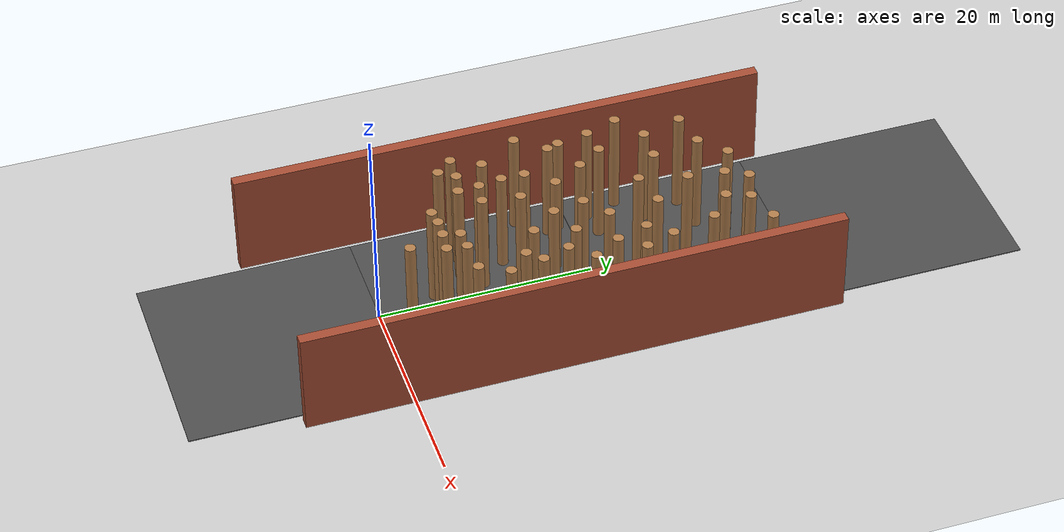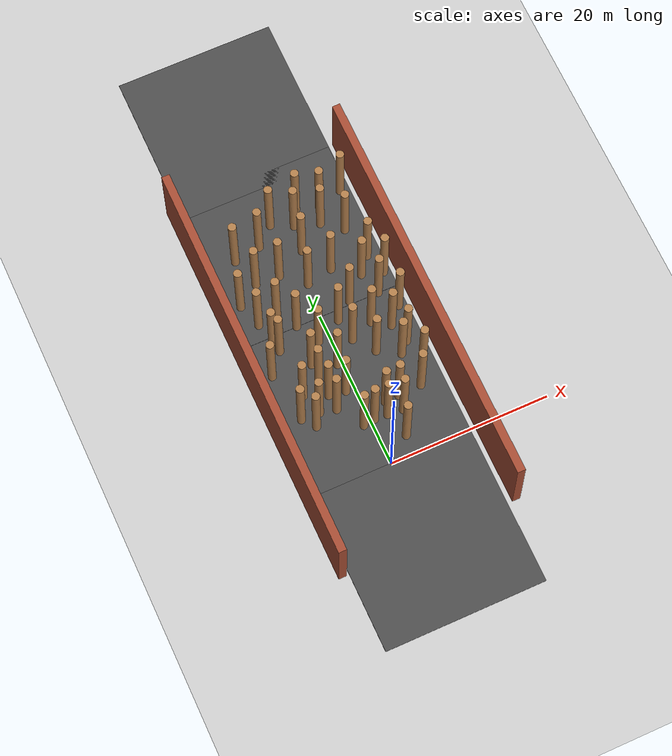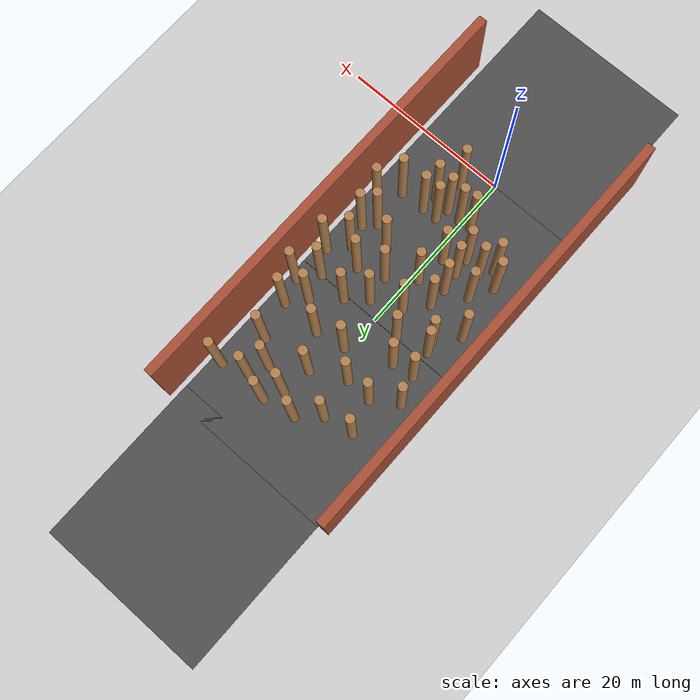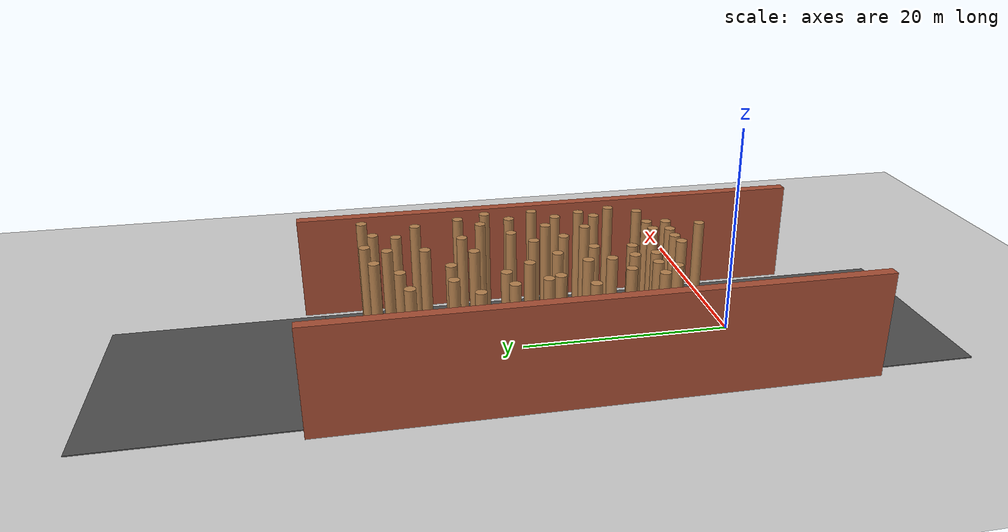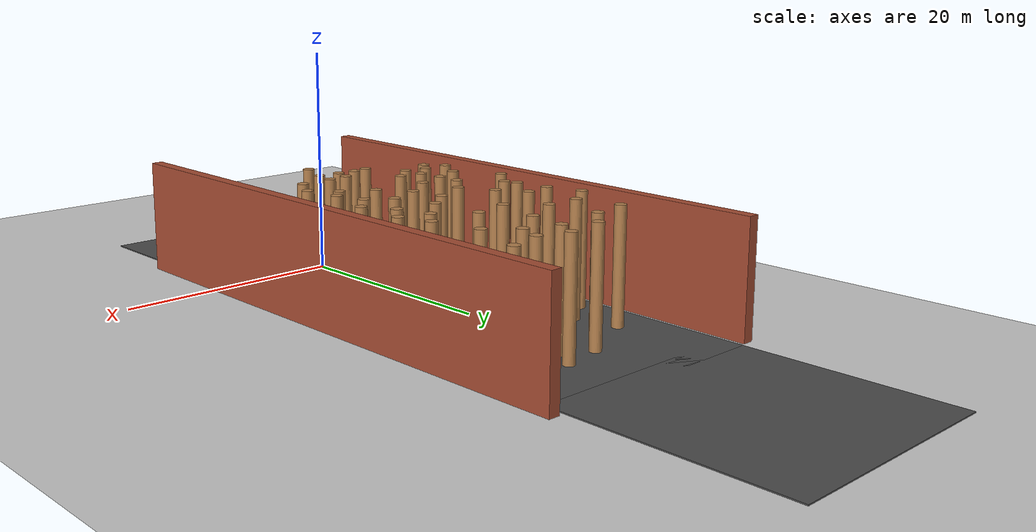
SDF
<sdf version="1.6">
 <world name="default">
  <light name="sun" type="directional">
   <pose>0 -10 10 0 -0 0</pose>
   <diffuse>0.8 0.8 0.8 1</diffuse>
   <specular>0.2 0.2 0.2 1</specular>
   <attenuation>
    <range>1000</range>
    <constant>0.9</constant>
    <linear>0.01</linear>
    <quadratic>0.001</quadratic>
   </attenuation>
   <direction>100 10 -10</direction>
  </light>
  <model name="ground_plane">
   <static>1</static>
   <link name="link">
    <collision name="collision">
     <geometry><plane><normal>0 0 1</normal><size>100 100</size></plane></geometry>
     <surface><friction><ode><mu>100</mu><mu2>50</mu2></ode></friction></surface>
    </collision>
    <visual name="visual">
     <cast_shadows>0</cast_shadows>
     <geometry><plane><normal>0 0 1</normal><size>100 100</size></plane></geometry>
     <material>
      <script><uri>file://media/materials/scripts/gazebo.material</uri><name>Gazebo/Grey</name></script>
     </material>
    </visual>
   </link>
  </model>
  <gravity>0 0 -9.8</gravity>
  <magnetic_field>6e-06 2.3e-05 -4.2e-05</magnetic_field>
  <atmosphere type="adiabatic"/>
  <physics name="default_physics" default="0" type="ode">
   <max_step_size>0.001</max_step_size>
   <real_time_factor>1</real_time_factor>
   <real_time_update_rate>1000</real_time_update_rate>
  </physics>
  <scene><ambient>0.4 0.4 0.4 1</ambient><background>0.7 0.7 0.7 1</background><shadows>1</shadows></scene>
  <spherical_coordinates>
   <surface_model>EARTH_WGS84</surface_model>
   <latitude_deg>0</latitude_deg>
   <longitude_deg>0</longitude_deg>
   <elevation>0</elevation>
   <heading_deg>0</heading_deg>
  </spherical_coordinates>
  <model name="asphalt_plane_1">
   <static>1</static>
   <link name="link">
    <collision name="collision"><geometry><box><size>20 20 0.1</size></box></geometry></collision>
    <visual name="visual">
     <cast_shadows>0</cast_shadows>
     <geometry><box><size>20 20 0.1</size></box></geometry>
     <material>
      <script>
       <uri>model://asphalt_plane/materials/scripts</uri>
       <uri>model://asphalt_plane/materials/textures</uri>
       <name>vrc/asphalt</name>
      </script>
     </material>
    </visual>
   </link>
   <pose>0.098004 9.97829 0 0 -0 0</pose>
  </model>
  <model name="asphalt_plane_2">
   <static>1</static>
   <link name="link">
    <collision name="collision"><geometry><box><size>20 20 0.1</size></box></geometry></collision>
    <visual name="visual">
     <cast_shadows>0</cast_shadows>
     <geometry><box><size>20 20 0.1</size></box></geometry>
     <material>
      <script>
       <uri>model://asphalt_plane/materials/scripts</uri>
       <uri>model://asphalt_plane/materials/textures</uri>
       <name>vrc/asphalt</name>
      </script>
     </material>
    </visual>
   </link>
   <pose>0.117642 29.9977 0 0 -0 0</pose>
  </model>
  <model name="asphalt_plane_3">
   <static>1</static>
   <link name="link">
    <collision name="collision"><geometry><box><size>20 20 0.1</size></box></geometry></collision>
    <visual name="visual">
     <cast_shadows>0</cast_shadows>
     <geometry><box><size>20 20 0.1</size></box></geometry>
     <material>
      <script>
       <uri>model://asphalt_plane/materials/scripts</uri>
       <uri>model://asphalt_plane/materials/textures</uri>
       <name>vrc/asphalt</name>
      </script>
     </material>
    </visual>
   </link>
   <pose>0.085062 -9.98607 0 0 -0 0</pose>
  </model>
  <model name="train_3">
   <link name="link_0_clone_0_clone_11">
    <pose>4.2784 -11.9007 0.043478 0 -0 0</pose>
    <inertial>
     <mass>1000</mass>
     <inertia><ixx>0.145833</ixx><ixy>0</ixy><ixz>0</ixz><iyy>0.145833</iyy><iyz>0</iyz><izz>0.125</izz></inertia>
    </inertial>
    <visual name="visual">
     <pose>0 0 4.5 0 -0 0</pose>
     <geometry><cylinder><radius>0.5</radius><length>10</length></cylinder></geometry>
     <material>
      <lighting>1</lighting>
      <script><uri>file://media/materials/scripts/gazebo.material</uri><name>Gazebo/WoodFloor</name></script>
      <ambient>0.3 0.3 0.3 1</ambient>
      <diffuse>0.7 0.7 0.7 1</diffuse>
      <specular>0.01 0.01 0.01 1</specular>
      <emissive>0 0 0 1</emissive>
      <shader type="vertex"><normal_map>__default__</normal_map></shader>
     </material>
    </visual>
    <collision name="collision">
     <pose>0 0 4.5 0 -0 0</pose>
     <geometry><cylinder><radius>0.5</radius><length>10</length></cylinder></geometry>
     <surface>
      <friction>
       <ode><mu>1</mu><mu2>1</mu2><fdir1>0 0 0</fdir1><slip1>0</slip1><slip2>0</slip2></ode>
       <torsional>
        <coefficient>1</coefficient>
        <patch_radius>0</patch_radius>
        <surface_radius>0</surface_radius>
        <use_patch_radius>1</use_patch_radius>
        <ode><slip>0</slip></ode>
       </torsional>
      </friction>
      <bounce><restitution_coefficient>0</restitution_coefficient><threshold>1e+06</threshold></bounce>
      <contact>
       <collide_without_contact>0</collide_without_contact>
       <collide_without_contact_bitmask>1</collide_without_contact_bitmask>
       <collide_bitmask>1</collide_bitmask>
       <ode>
        <soft_cfm>0</soft_cfm>
        <soft_erp>0.2</soft_erp>
        <kp>1e+13</kp>
        <kd>1</kd>
        <max_vel>0.01</max_vel>
        <min_depth>0</min_depth>
       </ode>
       <bullet>
        <split_impulse>1</split_impulse>
        <split_impulse_penetration_threshold>-0.01</split_impulse_penetration_threshold>
        <soft_cfm>0</soft_cfm>
        <soft_erp>0.2</soft_erp>
        <kp>1e+13</kp>
        <kd>1</kd>
       </bullet>
      </contact>
     </surface>
    </collision>
   </link>
   <link name="link_0_clone_0_clone_11_clone_19">
    <pose>7.08596 18.8441 0.043478 0 -0 3e-06</pose>
    <inertial>
     <mass>1000</mass>
     <inertia><ixx>0.145833</ixx><ixy>0</ixy><ixz>0</ixz><iyy>0.145833</iyy><iyz>0</iyz><izz>0.125</izz></inertia>
    </inertial>
    <visual name="visual">
     <pose>0 0 4.5 0 -0 0</pose>
     <geometry><cylinder><radius>0.5</radius><length>10</length></cylinder></geometry>
     <material>
      <lighting>1</lighting>
      <script><uri>file://media/materials/scripts/gazebo.material</uri><name>Gazebo/WoodFloor</name></script>
      <ambient>0.3 0.3 0.3 1</ambient>
      <diffuse>0.7 0.7 0.7 1</diffuse>
      <specular>0.01 0.01 0.01 1</specular>
      <emissive>0 0 0 1</emissive>
      <shader type="vertex"><normal_map>__default__</normal_map></shader>
     </material>
    </visual>
    <collision name="collision">
     <pose>0 0 4.5 0 -0 0</pose>
     <geometry><cylinder><radius>0.5</radius><length>10</length></cylinder></geometry>
     <surface>
      <friction>
       <ode><mu>1</mu><mu2>1</mu2><fdir1>0 0 0</fdir1><slip1>0</slip1><slip2>0</slip2></ode>
       <torsional>
        <coefficient>1</coefficient>
        <patch_radius>0</patch_radius>
        <surface_radius>0</surface_radius>
        <use_patch_radius>1</use_patch_radius>
        <ode><slip>0</slip></ode>
       </torsional>
      </friction>
      <bounce><restitution_coefficient>0</restitution_coefficient><threshold>1e+06</threshold></bounce>
      <contact>
       <collide_without_contact>0</collide_without_contact>
       <collide_without_contact_bitmask>1</collide_without_contact_bitmask>
       <collide_bitmask>1</collide_bitmask>
       <ode>
        <soft_cfm>0</soft_cfm>
        <soft_erp>0.2</soft_erp>
        <kp>1e+13</kp>
        <kd>1</kd>
        <max_vel>0.01</max_vel>
        <min_depth>0</min_depth>
       </ode>
       <bullet>
        <split_impulse>1</split_impulse>
        <split_impulse_penetration_threshold>-0.01</split_impulse_penetration_threshold>
        <soft_cfm>0</soft_cfm>
        <soft_erp>0.2</soft_erp>
        <kp>1e+13</kp>
        <kd>1</kd>
       </bullet>
      </contact>
     </surface>
    </collision>
   </link>
   <link name="link_0_clone_0_clone_11_clone_8">
    <pose>-6.90192 1.15105 0.043478 0 -0 3e-06</pose>
    <inertial>
     <mass>1000</mass>
     <inertia><ixx>0.145833</ixx><ixy>0</ixy><ixz>0</ixz><iyy>0.145833</iyy><iyz>0</iyz><izz>0.125</izz></inertia>
    </inertial>
    <visual name="visual">
     <pose>0 0 4.5 0 -0 0</pose>
     <geometry><cylinder><radius>0.5</radius><length>10</length></cylinder></geometry>
     <material>
      <lighting>1</lighting>
      <script><uri>file://media/materials/scripts/gazebo.material</uri><name>Gazebo/WoodFloor</name></script>
      <ambient>0.3 0.3 0.3 1</ambient>
      <diffuse>0.7 0.7 0.7 1</diffuse>
      <specular>0.01 0.01 0.01 1</specular>
      <emissive>0 0 0 1</emissive>
      <shader type="vertex"><normal_map>__default__</normal_map></shader>
     </material>
    </visual>
    <collision name="collision">
     <pose>0 0 4.5 0 -0 0</pose>
     <geometry><cylinder><radius>0.5</radius><length>10</length></cylinder></geometry>
     <surface>
      <friction>
       <ode><mu>1</mu><mu2>1</mu2><fdir1>0 0 0</fdir1><slip1>0</slip1><slip2>0</slip2></ode>
       <torsional>
        <coefficient>1</coefficient>
        <patch_radius>0</patch_radius>
        <surface_radius>0</surface_radius>
        <use_patch_radius>1</use_patch_radius>
        <ode><slip>0</slip></ode>
       </torsional>
      </friction>
      <bounce><restitution_coefficient>0</restitution_coefficient><threshold>1e+06</threshold></bounce>
      <contact>
       <collide_without_contact>0</collide_without_contact>
       <collide_without_contact_bitmask>1</collide_without_contact_bitmask>
       <collide_bitmask>1</collide_bitmask>
       <ode>
        <soft_cfm>0</soft_cfm>
        <soft_erp>0.2</soft_erp>
        <kp>1e+13</kp>
        <kd>1</kd>
        <max_vel>0.01</max_vel>
        <min_depth>0</min_depth>
       </ode>
       <bullet>
        <split_impulse>1</split_impulse>
        <split_impulse_penetration_threshold>-0.01</split_impulse_penetration_threshold>
        <soft_cfm>0</soft_cfm>
        <soft_erp>0.2</soft_erp>
        <kp>1e+13</kp>
        <kd>1</kd>
       </bullet>
      </contact>
     </surface>
    </collision>
   </link>
   <link name="link_0_clone_0_clone_16">
    <pose>-3.95167 12.6277 0.043478 0 -0 0</pose>
    <inertial>
     <mass>1000</mass>
     <inertia><ixx>0.145833</ixx><ixy>0</ixy><ixz>0</ixz><iyy>0.145833</iyy><iyz>0</iyz><izz>0.125</izz></inertia>
    </inertial>
    <visual name="visual">
     <pose>0 0 4.5 0 -0 0</pose>
     <geometry><cylinder><radius>0.5</radius><length>10</length></cylinder></geometry>
     <material>
      <lighting>1</lighting>
      <script><uri>file://media/materials/scripts/gazebo.material</uri><name>Gazebo/WoodFloor</name></script>
      <ambient>0.3 0.3 0.3 1</ambient>
      <diffuse>0.7 0.7 0.7 1</diffuse>
      <specular>0.01 0.01 0.01 1</specular>
      <emissive>0 0 0 1</emissive>
      <shader type="vertex"><normal_map>__default__</normal_map></shader>
     </material>
    </visual>
    <collision name="collision">
     <pose>0 0 4.5 0 -0 0</pose>
     <geometry><cylinder><radius>0.5</radius><length>10</length></cylinder></geometry>
     <surface>
      <friction>
       <ode><mu>1</mu><mu2>1</mu2><fdir1>0 0 0</fdir1><slip1>0</slip1><slip2>0</slip2></ode>
       <torsional>
        <coefficient>1</coefficient>
        <patch_radius>0</patch_radius>
        <surface_radius>0</surface_radius>
        <use_patch_radius>1</use_patch_radius>
        <ode><slip>0</slip></ode>
       </torsional>
      </friction>
      <bounce><restitution_coefficient>0</restitution_coefficient><threshold>1e+06</threshold></bounce>
      <contact>
       <collide_without_contact>0</collide_without_contact>
       <collide_without_contact_bitmask>1</collide_without_contact_bitmask>
       <collide_bitmask>1</collide_bitmask>
       <ode>
        <soft_cfm>0</soft_cfm>
        <soft_erp>0.2</soft_erp>
        <kp>1e+13</kp>
        <kd>1</kd>
        <max_vel>0.01</max_vel>
        <min_depth>0</min_depth>
       </ode>
       <bullet>
        <split_impulse>1</split_impulse>
        <split_impulse_penetration_threshold>-0.01</split_impulse_penetration_threshold>
        <soft_cfm>0</soft_cfm>
        <soft_erp>0.2</soft_erp>
        <kp>1e+13</kp>
        <kd>1</kd>
       </bullet>
      </contact>
     </surface>
    </collision>
   </link>
   <link name="link_0_clone_0_clone_5_clone_1">
    <pose>5.55345 -7.0629 0.043478 0 -0 3e-06</pose>
    <inertial>
     <mass>1000</mass>
     <inertia><ixx>0.145833</ixx><ixy>0</ixy><ixz>0</ixz><iyy>0.145833</iyy><iyz>0</iyz><izz>0.125</izz></inertia>
    </inertial>
    <visual name="visual">
     <pose>0 0 4.5 0 -0 0</pose>
     <geometry><cylinder><radius>0.5</radius><length>10</length></cylinder></geometry>
     <material>
      <lighting>1</lighting>
      <script><uri>file://media/materials/scripts/gazebo.material</uri><name>Gazebo/WoodFloor</name></script>
      <ambient>0.3 0.3 0.3 1</ambient>
      <diffuse>0.7 0.7 0.7 1</diffuse>
      <specular>0.01 0.01 0.01 1</specular>
      <emissive>0 0 0 1</emissive>
      <shader type="vertex"><normal_map>__default__</normal_map></shader>
     </material>
    </visual>
    <collision name="collision">
     <pose>0 0 4.5 0 -0 0</pose>
     <geometry><cylinder><radius>0.5</radius><length>10</length></cylinder></geometry>
     <surface>
      <friction>
       <ode><mu>1</mu><mu2>1</mu2><fdir1>0 0 0</fdir1><slip1>0</slip1><slip2>0</slip2></ode>
       <torsional>
        <coefficient>1</coefficient>
        <patch_radius>0</patch_radius>
        <surface_radius>0</surface_radius>
        <use_patch_radius>1</use_patch_radius>
        <ode><slip>0</slip></ode>
       </torsional>
      </friction>
      <bounce><restitution_coefficient>0</restitution_coefficient><threshold>1e+06</threshold></bounce>
      <contact>
       <collide_without_contact>0</collide_without_contact>
       <collide_without_contact_bitmask>1</collide_without_contact_bitmask>
       <collide_bitmask>1</collide_bitmask>
       <ode>
        <soft_cfm>0</soft_cfm>
        <soft_erp>0.2</soft_erp>
        <kp>1e+13</kp>
        <kd>1</kd>
        <max_vel>0.01</max_vel>
        <min_depth>0</min_depth>
       </ode>
       <bullet>
        <split_impulse>1</split_impulse>
        <split_impulse_penetration_threshold>-0.01</split_impulse_penetration_threshold>
        <soft_cfm>0</soft_cfm>
        <soft_erp>0.2</soft_erp>
        <kp>1e+13</kp>
        <kd>1</kd>
       </bullet>
      </contact>
     </surface>
    </collision>
   </link>
   <link name="link_0_clone_0_clone_5_clone_12">
    <pose>3.06332 4.4517 0.043478 0 -0 3e-06</pose>
    <inertial>
     <mass>1000</mass>
     <inertia><ixx>0.145833</ixx><ixy>0</ixy><ixz>0</ixz><iyy>0.145833</iyy><iyz>0</iyz><izz>0.125</izz></inertia>
    </inertial>
    <visual name="visual">
     <pose>0 0 4.5 0 -0 0</pose>
     <geometry><cylinder><radius>0.5</radius><length>10</length></cylinder></geometry>
     <material>
      <lighting>1</lighting>
      <script><uri>file://media/materials/scripts/gazebo.material</uri><name>Gazebo/WoodFloor</name></script>
      <ambient>0.3 0.3 0.3 1</ambient>
      <diffuse>0.7 0.7 0.7 1</diffuse>
      <specular>0.01 0.01 0.01 1</specular>
      <emissive>0 0 0 1</emissive>
      <shader type="vertex"><normal_map>__default__</normal_map></shader>
     </material>
    </visual>
    <collision name="collision">
     <pose>0 0 4.5 0 -0 0</pose>
     <geometry><cylinder><radius>0.5</radius><length>10</length></cylinder></geometry>
     <surface>
      <friction>
       <ode><mu>1</mu><mu2>1</mu2><fdir1>0 0 0</fdir1><slip1>0</slip1><slip2>0</slip2></ode>
       <torsional>
        <coefficient>1</coefficient>
        <patch_radius>0</patch_radius>
        <surface_radius>0</surface_radius>
        <use_patch_radius>1</use_patch_radius>
        <ode><slip>0</slip></ode>
       </torsional>
      </friction>
      <bounce><restitution_coefficient>0</restitution_coefficient><threshold>1e+06</threshold></bounce>
      <contact>
       <collide_without_contact>0</collide_without_contact>
       <collide_without_contact_bitmask>1</collide_without_contact_bitmask>
       <collide_bitmask>1</collide_bitmask>
       <ode>
        <soft_cfm>0</soft_cfm>
        <soft_erp>0.2</soft_erp>
        <kp>1e+13</kp>
        <kd>1</kd>
        <max_vel>0.01</max_vel>
        <min_depth>0</min_depth>
       </ode>
       <bullet>
        <split_impulse>1</split_impulse>
        <split_impulse_penetration_threshold>-0.01</split_impulse_penetration_threshold>
        <soft_cfm>0</soft_cfm>
        <soft_erp>0.2</soft_erp>
        <kp>1e+13</kp>
        <kd>1</kd>
       </bullet>
      </contact>
     </surface>
    </collision>
   </link>
   <link name="link_0_clone_0_clone_5_clone_18">
    <pose>0.694929 19.0204 0.043478 0 -0 3e-06</pose>
    <inertial>
     <mass>1000</mass>
     <inertia><ixx>0.145833</ixx><ixy>0</ixy><ixz>0</ixz><iyy>0.145833</iyy><iyz>0</iyz><izz>0.125</izz></inertia>
    </inertial>
    <visual name="visual">
     <pose>0 0 4.5 0 -0 0</pose>
     <geometry><cylinder><radius>0.5</radius><length>10</length></cylinder></geometry>
     <material>
      <lighting>1</lighting>
      <script><uri>file://media/materials/scripts/gazebo.material</uri><name>Gazebo/WoodFloor</name></script>
      <ambient>0.3 0.3 0.3 1</ambient>
      <diffuse>0.7 0.7 0.7 1</diffuse>
      <specular>0.01 0.01 0.01 1</specular>
      <emissive>0 0 0 1</emissive>
      <shader type="vertex"><normal_map>__default__</normal_map></shader>
     </material>
    </visual>
    <collision name="collision">
     <pose>0 0 4.5 0 -0 0</pose>
     <geometry><cylinder><radius>0.5</radius><length>10</length></cylinder></geometry>
     <surface>
      <friction>
       <ode><mu>1</mu><mu2>1</mu2><fdir1>0 0 0</fdir1><slip1>0</slip1><slip2>0</slip2></ode>
       <torsional>
        <coefficient>1</coefficient>
        <patch_radius>0</patch_radius>
        <surface_radius>0</surface_radius>
        <use_patch_radius>1</use_patch_radius>
        <ode><slip>0</slip></ode>
       </torsional>
      </friction>
      <bounce><restitution_coefficient>0</restitution_coefficient><threshold>1e+06</threshold></bounce>
      <contact>
       <collide_without_contact>0</collide_without_contact>
       <collide_without_contact_bitmask>1</collide_without_contact_bitmask>
       <collide_bitmask>1</collide_bitmask>
       <ode>
        <soft_cfm>0</soft_cfm>
        <soft_erp>0.2</soft_erp>
        <kp>1e+13</kp>
        <kd>1</kd>
        <max_vel>0.01</max_vel>
        <min_depth>0</min_depth>
       </ode>
       <bullet>
        <split_impulse>1</split_impulse>
        <split_impulse_penetration_threshold>-0.01</split_impulse_penetration_threshold>
        <soft_cfm>0</soft_cfm>
        <soft_erp>0.2</soft_erp>
        <kp>1e+13</kp>
        <kd>1</kd>
       </bullet>
      </contact>
     </surface>
    </collision>
   </link>
   <link name="link_0_clone_0_clone_5_clone_19">
    <pose>-4.98555 16.3648 0.043478 0 -0 3e-06</pose>
    <inertial>
     <mass>1000</mass>
     <inertia><ixx>0.145833</ixx><ixy>0</ixy><ixz>0</ixz><iyy>0.145833</iyy><iyz>0</iyz><izz>0.125</izz></inertia>
    </inertial>
    <visual name="visual">
     <pose>0 0 4.5 0 -0 0</pose>
     <geometry><cylinder><radius>0.5</radius><length>10</length></cylinder></geometry>
     <material>
      <lighting>1</lighting>
      <script><uri>file://media/materials/scripts/gazebo.material</uri><name>Gazebo/WoodFloor</name></script>
      <ambient>0.3 0.3 0.3 1</ambient>
      <diffuse>0.7 0.7 0.7 1</diffuse>
      <specular>0.01 0.01 0.01 1</specular>
      <emissive>0 0 0 1</emissive>
      <shader type="vertex"><normal_map>__default__</normal_map></shader>
     </material>
    </visual>
    <collision name="collision">
     <pose>0 0 4.5 0 -0 0</pose>
     <geometry><cylinder><radius>0.5</radius><length>10</length></cylinder></geometry>
     <surface>
      <friction>
       <ode><mu>1</mu><mu2>1</mu2><fdir1>0 0 0</fdir1><slip1>0</slip1><slip2>0</slip2></ode>
       <torsional>
        <coefficient>1</coefficient>
        <patch_radius>0</patch_radius>
        <surface_radius>0</surface_radius>
        <use_patch_radius>1</use_patch_radius>
        <ode><slip>0</slip></ode>
       </torsional>
      </friction>
      <bounce><restitution_coefficient>0</restitution_coefficient><threshold>1e+06</threshold></bounce>
      <contact>
       <collide_without_contact>0</collide_without_contact>
       <collide_without_contact_bitmask>1</collide_without_contact_bitmask>
       <collide_bitmask>1</collide_bitmask>
       <ode>
        <soft_cfm>0</soft_cfm>
        <soft_erp>0.2</soft_erp>
        <kp>1e+13</kp>
        <kd>1</kd>
        <max_vel>0.01</max_vel>
        <min_depth>0</min_depth>
       </ode>
       <bullet>
        <split_impulse>1</split_impulse>
        <split_impulse_penetration_threshold>-0.01</split_impulse_penetration_threshold>
        <soft_cfm>0</soft_cfm>
        <soft_erp>0.2</soft_erp>
        <kp>1e+13</kp>
        <kd>1</kd>
       </bullet>
      </contact>
     </surface>
    </collision>
   </link>
   <link name="link_0_clone_0_clone_5_clone_19_clone">
    <pose>-0.976364 12.5026 0.043478 0 -0 6e-06</pose>
    <inertial>
     <mass>1000</mass>
     <inertia><ixx>0.145833</ixx><ixy>0</ixy><ixz>0</ixz><iyy>0.145833</iyy><iyz>0</iyz><izz>0.125</izz></inertia>
    </inertial>
    <visual name="visual">
     <pose>0 0 4.5 0 -0 0</pose>
     <geometry><cylinder><radius>0.5</radius><length>10</length></cylinder></geometry>
     <material>
      <lighting>1</lighting>
      <script><uri>file://media/materials/scripts/gazebo.material</uri><name>Gazebo/WoodFloor</name></script>
      <ambient>0.3 0.3 0.3 1</ambient>
      <diffuse>0.7 0.7 0.7 1</diffuse>
      <specular>0.01 0.01 0.01 1</specular>
      <emissive>0 0 0 1</emissive>
      <shader type="vertex"><normal_map>__default__</normal_map></shader>
     </material>
    </visual>
    <collision name="collision">
     <pose>0 0 4.5 0 -0 0</pose>
     <geometry><cylinder><radius>0.5</radius><length>10</length></cylinder></geometry>
     <surface>
      <friction>
       <ode><mu>1</mu><mu2>1</mu2><fdir1>0 0 0</fdir1><slip1>0</slip1><slip2>0</slip2></ode>
       <torsional>
        <coefficient>1</coefficient>
        <patch_radius>0</patch_radius>
        <surface_radius>0</surface_radius>
        <use_patch_radius>1</use_patch_radius>
        <ode><slip>0</slip></ode>
       </torsional>
      </friction>
      <bounce><restitution_coefficient>0</restitution_coefficient><threshold>1e+06</threshold></bounce>
      <contact>
       <collide_without_contact>0</collide_without_contact>
       <collide_without_contact_bitmask>1</collide_without_contact_bitmask>
       <collide_bitmask>1</collide_bitmask>
       <ode>
        <soft_cfm>0</soft_cfm>
        <soft_erp>0.2</soft_erp>
        <kp>1e+13</kp>
        <kd>1</kd>
        <max_vel>0.01</max_vel>
        <min_depth>0</min_depth>
       </ode>
       <bullet>
        <split_impulse>1</split_impulse>
        <split_impulse_penetration_threshold>-0.01</split_impulse_penetration_threshold>
        <soft_cfm>0</soft_cfm>
        <soft_erp>0.2</soft_erp>
        <kp>1e+13</kp>
        <kd>1</kd>
       </bullet>
      </contact>
     </surface>
    </collision>
   </link>
   <link name="link_0_clone_0_clone_5_clone_19_clone_10">
    <pose>-5.21019 4.79116 0.043478 0 -0 6e-06</pose>
    <inertial>
     <mass>1000</mass>
     <inertia><ixx>0.145833</ixx><ixy>0</ixy><ixz>0</ixz><iyy>0.145833</iyy><iyz>0</iyz><izz>0.125</izz></inertia>
    </inertial>
    <visual name="visual">
     <pose>0 0 4.5 0 -0 0</pose>
     <geometry><cylinder><radius>0.5</radius><length>10</length></cylinder></geometry>
     <material>
      <lighting>1</lighting>
      <script><uri>file://media/materials/scripts/gazebo.material</uri><name>Gazebo/WoodFloor</name></script>
      <ambient>0.3 0.3 0.3 1</ambient>
      <diffuse>0.7 0.7 0.7 1</diffuse>
      <specular>0.01 0.01 0.01 1</specular>
      <emissive>0 0 0 1</emissive>
      <shader type="vertex"><normal_map>__default__</normal_map></shader>
     </material>
    </visual>
    <collision name="collision">
     <pose>0 0 4.5 0 -0 0</pose>
     <geometry><cylinder><radius>0.5</radius><length>10</length></cylinder></geometry>
     <surface>
      <friction>
       <ode><mu>1</mu><mu2>1</mu2><fdir1>0 0 0</fdir1><slip1>0</slip1><slip2>0</slip2></ode>
       <torsional>
        <coefficient>1</coefficient>
        <patch_radius>0</patch_radius>
        <surface_radius>0</surface_radius>
        <use_patch_radius>1</use_patch_radius>
        <ode><slip>0</slip></ode>
       </torsional>
      </friction>
      <bounce><restitution_coefficient>0</restitution_coefficient><threshold>1e+06</threshold></bounce>
      <contact>
       <collide_without_contact>0</collide_without_contact>
       <collide_without_contact_bitmask>1</collide_without_contact_bitmask>
       <collide_bitmask>1</collide_bitmask>
       <ode>
        <soft_cfm>0</soft_cfm>
        <soft_erp>0.2</soft_erp>
        <kp>1e+13</kp>
        <kd>1</kd>
        <max_vel>0.01</max_vel>
        <min_depth>0</min_depth>
       </ode>
       <bullet>
        <split_impulse>1</split_impulse>
        <split_impulse_penetration_threshold>-0.01</split_impulse_penetration_threshold>
        <soft_cfm>0</soft_cfm>
        <soft_erp>0.2</soft_erp>
        <kp>1e+13</kp>
        <kd>1</kd>
       </bullet>
      </contact>
     </surface>
    </collision>
   </link>
   <link name="link_0_clone_0_clone_5_clone_19_clone_11">
    <pose>-4.81689 3.68 0.043478 0 -0 6e-06</pose>
    <inertial>
     <mass>1000</mass>
     <inertia><ixx>0.145833</ixx><ixy>0</ixy><ixz>0</ixz><iyy>0.145833</iyy><iyz>0</iyz><izz>0.125</izz></inertia>
    </inertial>
    <visual name="visual">
     <pose>0 0 4.5 0 -0 0</pose>
     <geometry><cylinder><radius>0.5</radius><length>10</length></cylinder></geometry>
     <material>
      <lighting>1</lighting>
      <script><uri>file://media/materials/scripts/gazebo.material</uri><name>Gazebo/WoodFloor</name></script>
      <ambient>0.3 0.3 0.3 1</ambient>
      <diffuse>0.7 0.7 0.7 1</diffuse>
      <specular>0.01 0.01 0.01 1</specular>
      <emissive>0 0 0 1</emissive>
      <shader type="vertex"><normal_map>__default__</normal_map></shader>
     </material>
    </visual>
    <collision name="collision">
     <pose>0 0 4.5 0 -0 0</pose>
     <geometry><cylinder><radius>0.5</radius><length>10</length></cylinder></geometry>
     <surface>
      <friction>
       <ode><mu>1</mu><mu2>1</mu2><fdir1>0 0 0</fdir1><slip1>0</slip1><slip2>0</slip2></ode>
       <torsional>
        <coefficient>1</coefficient>
        <patch_radius>0</patch_radius>
        <surface_radius>0</surface_radius>
        <use_patch_radius>1</use_patch_radius>
        <ode><slip>0</slip></ode>
       </torsional>
      </friction>
      <bounce><restitution_coefficient>0</restitution_coefficient><threshold>1e+06</threshold></bounce>
      <contact>
       <collide_without_contact>0</collide_without_contact>
       <collide_without_contact_bitmask>1</collide_without_contact_bitmask>
       <collide_bitmask>1</collide_bitmask>
       <ode>
        <soft_cfm>0</soft_cfm>
        <soft_erp>0.2</soft_erp>
        <kp>1e+13</kp>
        <kd>1</kd>
        <max_vel>0.01</max_vel>
        <min_depth>0</min_depth>
       </ode>
       <bullet>
        <split_impulse>1</split_impulse>
        <split_impulse_penetration_threshold>-0.01</split_impulse_penetration_threshold>
        <soft_cfm>0</soft_cfm>
        <soft_erp>0.2</soft_erp>
        <kp>1e+13</kp>
        <kd>1</kd>
       </bullet>
      </contact>
     </surface>
    </collision>
   </link>
   <link name="link_0_clone_0_clone_5_clone_19_clone_12">
    <pose>-3.25564 8.05891 0.043478 0 -0 6e-06</pose>
    <inertial>
     <mass>1000</mass>
     <inertia><ixx>0.145833</ixx><ixy>0</ixy><ixz>0</ixz><iyy>0.145833</iyy><iyz>0</iyz><izz>0.125</izz></inertia>
    </inertial>
    <visual name="visual">
     <pose>0 0 4.5 0 -0 0</pose>
     <geometry><cylinder><radius>0.5</radius><length>10</length></cylinder></geometry>
     <material>
      <lighting>1</lighting>
      <script><uri>file://media/materials/scripts/gazebo.material</uri><name>Gazebo/WoodFloor</name></script>
      <ambient>0.3 0.3 0.3 1</ambient>
      <diffuse>0.7 0.7 0.7 1</diffuse>
      <specular>0.01 0.01 0.01 1</specular>
      <emissive>0 0 0 1</emissive>
      <shader type="vertex"><normal_map>__default__</normal_map></shader>
     </material>
    </visual>
    <collision name="collision">
     <pose>0 0 4.5 0 -0 0</pose>
     <geometry><cylinder><radius>0.5</radius><length>10</length></cylinder></geometry>
     <surface>
      <friction>
       <ode><mu>1</mu><mu2>1</mu2><fdir1>0 0 0</fdir1><slip1>0</slip1><slip2>0</slip2></ode>
       <torsional>
        <coefficient>1</coefficient>
        <patch_radius>0</patch_radius>
        <surface_radius>0</surface_radius>
        <use_patch_radius>1</use_patch_radius>
        <ode><slip>0</slip></ode>
       </torsional>
      </friction>
      <bounce><restitution_coefficient>0</restitution_coefficient><threshold>1e+06</threshold></bounce>
      <contact>
       <collide_without_contact>0</collide_without_contact>
       <collide_without_contact_bitmask>1</collide_without_contact_bitmask>
       <collide_bitmask>1</collide_bitmask>
       <ode>
        <soft_cfm>0</soft_cfm>
        <soft_erp>0.2</soft_erp>
        <kp>1e+13</kp>
        <kd>1</kd>
        <max_vel>0.01</max_vel>
        <min_depth>0</min_depth>
       </ode>
       <bullet>
        <split_impulse>1</split_impulse>
        <split_impulse_penetration_threshold>-0.01</split_impulse_penetration_threshold>
        <soft_cfm>0</soft_cfm>
        <soft_erp>0.2</soft_erp>
        <kp>1e+13</kp>
        <kd>1</kd>
       </bullet>
      </contact>
     </surface>
    </collision>
   </link>
   <link name="link_0_clone_0_clone_5_clone_19_clone_13">
    <pose>5.27392 6.1772 0.043478 0 -0 6e-06</pose>
    <inertial>
     <mass>1000</mass>
     <inertia><ixx>0.145833</ixx><ixy>0</ixy><ixz>0</ixz><iyy>0.145833</iyy><iyz>0</iyz><izz>0.125</izz></inertia>
    </inertial>
    <visual name="visual">
     <pose>0 0 4.5 0 -0 0</pose>
     <geometry><cylinder><radius>0.5</radius><length>10</length></cylinder></geometry>
     <material>
      <lighting>1</lighting>
      <script><uri>file://media/materials/scripts/gazebo.material</uri><name>Gazebo/WoodFloor</name></script>
      <ambient>0.3 0.3 0.3 1</ambient>
      <diffuse>0.7 0.7 0.7 1</diffuse>
      <specular>0.01 0.01 0.01 1</specular>
      <emissive>0 0 0 1</emissive>
      <shader type="vertex"><normal_map>__default__</normal_map></shader>
     </material>
    </visual>
    <collision name="collision">
     <pose>0 0 4.5 0 -0 0</pose>
     <geometry><cylinder><radius>0.5</radius><length>10</length></cylinder></geometry>
     <surface>
      <friction>
       <ode><mu>1</mu><mu2>1</mu2><fdir1>0 0 0</fdir1><slip1>0</slip1><slip2>0</slip2></ode>
       <torsional>
        <coefficient>1</coefficient>
        <patch_radius>0</patch_radius>
        <surface_radius>0</surface_radius>
        <use_patch_radius>1</use_patch_radius>
        <ode><slip>0</slip></ode>
       </torsional>
      </friction>
      <bounce><restitution_coefficient>0</restitution_coefficient><threshold>1e+06</threshold></bounce>
      <contact>
       <collide_without_contact>0</collide_without_contact>
       <collide_without_contact_bitmask>1</collide_without_contact_bitmask>
       <collide_bitmask>1</collide_bitmask>
       <ode>
        <soft_cfm>0</soft_cfm>
        <soft_erp>0.2</soft_erp>
        <kp>1e+13</kp>
        <kd>1</kd>
        <max_vel>0.01</max_vel>
        <min_depth>0</min_depth>
       </ode>
       <bullet>
        <split_impulse>1</split_impulse>
        <split_impulse_penetration_threshold>-0.01</split_impulse_penetration_threshold>
        <soft_cfm>0</soft_cfm>
        <soft_erp>0.2</soft_erp>
        <kp>1e+13</kp>
        <kd>1</kd>
       </bullet>
      </contact>
     </surface>
    </collision>
   </link>
   <link name="link_0_clone_0_clone_5_clone_19_clone_15">
    <pose>8.82989 5.75323 0.043478 0 -0 6e-06</pose>
    <inertial>
     <mass>1000</mass>
     <inertia><ixx>0.145833</ixx><ixy>0</ixy><ixz>0</ixz><iyy>0.145833</iyy><iyz>0</iyz><izz>0.125</izz></inertia>
    </inertial>
    <visual name="visual">
     <pose>0 0 4.5 0 -0 0</pose>
     <geometry><cylinder><radius>0.5</radius><length>10</length></cylinder></geometry>
     <material>
      <lighting>1</lighting>
      <script><uri>file://media/materials/scripts/gazebo.material</uri><name>Gazebo/WoodFloor</name></script>
      <ambient>0.3 0.3 0.3 1</ambient>
      <diffuse>0.7 0.7 0.7 1</diffuse>
      <specular>0.01 0.01 0.01 1</specular>
      <emissive>0 0 0 1</emissive>
      <shader type="vertex"><normal_map>__default__</normal_map></shader>
     </material>
    </visual>
    <collision name="collision">
     <pose>0 0 4.5 0 -0 0</pose>
     <geometry><cylinder><radius>0.5</radius><length>10</length></cylinder></geometry>
     <surface>
      <friction>
       <ode><mu>1</mu><mu2>1</mu2><fdir1>0 0 0</fdir1><slip1>0</slip1><slip2>0</slip2></ode>
       <torsional>
        <coefficient>1</coefficient>
        <patch_radius>0</patch_radius>
        <surface_radius>0</surface_radius>
        <use_patch_radius>1</use_patch_radius>
        <ode><slip>0</slip></ode>
       </torsional>
      </friction>
      <bounce><restitution_coefficient>0</restitution_coefficient><threshold>1e+06</threshold></bounce>
      <contact>
       <collide_without_contact>0</collide_without_contact>
       <collide_without_contact_bitmask>1</collide_without_contact_bitmask>
       <collide_bitmask>1</collide_bitmask>
       <ode>
        <soft_cfm>0</soft_cfm>
        <soft_erp>0.2</soft_erp>
        <kp>1e+13</kp>
        <kd>1</kd>
        <max_vel>0.01</max_vel>
        <min_depth>0</min_depth>
       </ode>
       <bullet>
        <split_impulse>1</split_impulse>
        <split_impulse_penetration_threshold>-0.01</split_impulse_penetration_threshold>
        <soft_cfm>0</soft_cfm>
        <soft_erp>0.2</soft_erp>
        <kp>1e+13</kp>
        <kd>1</kd>
       </bullet>
      </contact>
     </surface>
    </collision>
   </link>
   <link name="link_0_clone_0_clone_5_clone_19_clone_16">
    <pose>10.5244 7.88191 0.043478 0 -0 6e-06</pose>
    <inertial>
     <mass>1000</mass>
     <inertia><ixx>0.145833</ixx><ixy>0</ixy><ixz>0</ixz><iyy>0.145833</iyy><iyz>0</iyz><izz>0.125</izz></inertia>
    </inertial>
    <visual name="visual">
     <pose>0 0 4.5 0 -0 0</pose>
     <geometry><cylinder><radius>0.5</radius><length>10</length></cylinder></geometry>
     <material>
      <lighting>1</lighting>
      <script><uri>file://media/materials/scripts/gazebo.material</uri><name>Gazebo/WoodFloor</name></script>
      <ambient>0.3 0.3 0.3 1</ambient>
      <diffuse>0.7 0.7 0.7 1</diffuse>
      <specular>0.01 0.01 0.01 1</specular>
      <emissive>0 0 0 1</emissive>
      <shader type="vertex"><normal_map>__default__</normal_map></shader>
     </material>
    </visual>
    <collision name="collision">
     <pose>0 0 4.5 0 -0 0</pose>
     <geometry><cylinder><radius>0.5</radius><length>10</length></cylinder></geometry>
     <surface>
      <friction>
       <ode><mu>1</mu><mu2>1</mu2><fdir1>0 0 0</fdir1><slip1>0</slip1><slip2>0</slip2></ode>
       <torsional>
        <coefficient>1</coefficient>
        <patch_radius>0</patch_radius>
        <surface_radius>0</surface_radius>
        <use_patch_radius>1</use_patch_radius>
        <ode><slip>0</slip></ode>
       </torsional>
      </friction>
      <bounce><restitution_coefficient>0</restitution_coefficient><threshold>1e+06</threshold></bounce>
      <contact>
       <collide_without_contact>0</collide_without_contact>
       <collide_without_contact_bitmask>1</collide_without_contact_bitmask>
       <collide_bitmask>1</collide_bitmask>
       <ode>
        <soft_cfm>0</soft_cfm>
        <soft_erp>0.2</soft_erp>
        <kp>1e+13</kp>
        <kd>1</kd>
        <max_vel>0.01</max_vel>
        <min_depth>0</min_depth>
       </ode>
       <bullet>
        <split_impulse>1</split_impulse>
        <split_impulse_penetration_threshold>-0.01</split_impulse_penetration_threshold>
        <soft_cfm>0</soft_cfm>
        <soft_erp>0.2</soft_erp>
        <kp>1e+13</kp>
        <kd>1</kd>
       </bullet>
      </contact>
     </surface>
    </collision>
   </link>
   <link name="link_0_clone_0_clone_5_clone_19_clone_18">
    <pose>10.335 3.24333 0.043478 0 -0 6e-06</pose>
    <inertial>
     <mass>1000</mass>
     <inertia><ixx>0.145833</ixx><ixy>0</ixy><ixz>0</ixz><iyy>0.145833</iyy><iyz>0</iyz><izz>0.125</izz></inertia>
    </inertial>
    <visual name="visual">
     <pose>0 0 4.5 0 -0 0</pose>
     <geometry><cylinder><radius>0.5</radius><length>10</length></cylinder></geometry>
     <material>
      <lighting>1</lighting>
      <script><uri>file://media/materials/scripts/gazebo.material</uri><name>Gazebo/WoodFloor</name></script>
      <ambient>0.3 0.3 0.3 1</ambient>
      <diffuse>0.7 0.7 0.7 1</diffuse>
      <specular>0.01 0.01 0.01 1</specular>
      <emissive>0 0 0 1</emissive>
      <shader type="vertex"><normal_map>__default__</normal_map></shader>
     </material>
    </visual>
    <collision name="collision">
     <pose>0 0 4.5 0 -0 0</pose>
     <geometry><cylinder><radius>0.5</radius><length>10</length></cylinder></geometry>
     <surface>
      <friction>
       <ode><mu>1</mu><mu2>1</mu2><fdir1>0 0 0</fdir1><slip1>0</slip1><slip2>0</slip2></ode>
       <torsional>
        <coefficient>1</coefficient>
        <patch_radius>0</patch_radius>
        <surface_radius>0</surface_radius>
        <use_patch_radius>1</use_patch_radius>
        <ode><slip>0</slip></ode>
       </torsional>
      </friction>
      <bounce><restitution_coefficient>0</restitution_coefficient><threshold>1e+06</threshold></bounce>
      <contact>
       <collide_without_contact>0</collide_without_contact>
       <collide_without_contact_bitmask>1</collide_without_contact_bitmask>
       <collide_bitmask>1</collide_bitmask>
       <ode>
        <soft_cfm>0</soft_cfm>
        <soft_erp>0.2</soft_erp>
        <kp>1e+13</kp>
        <kd>1</kd>
        <max_vel>0.01</max_vel>
        <min_depth>0</min_depth>
       </ode>
       <bullet>
        <split_impulse>1</split_impulse>
        <split_impulse_penetration_threshold>-0.01</split_impulse_penetration_threshold>
        <soft_cfm>0</soft_cfm>
        <soft_erp>0.2</soft_erp>
        <kp>1e+13</kp>
        <kd>1</kd>
       </bullet>
      </contact>
     </surface>
    </collision>
   </link>
   <link name="link_0_clone_0_clone_5_clone_19_clone_2">
    <pose>4.96938 10.8147 0.043478 0 -0 6e-06</pose>
    <inertial>
     <mass>1000</mass>
     <inertia><ixx>0.145833</ixx><ixy>0</ixy><ixz>0</ixz><iyy>0.145833</iyy><iyz>0</iyz><izz>0.125</izz></inertia>
    </inertial>
    <visual name="visual">
     <pose>0 0 4.5 0 -0 0</pose>
     <geometry><cylinder><radius>0.5</radius><length>10</length></cylinder></geometry>
     <material>
      <lighting>1</lighting>
      <script><uri>file://media/materials/scripts/gazebo.material</uri><name>Gazebo/WoodFloor</name></script>
      <ambient>0.3 0.3 0.3 1</ambient>
      <diffuse>0.7 0.7 0.7 1</diffuse>
      <specular>0.01 0.01 0.01 1</specular>
      <emissive>0 0 0 1</emissive>
      <shader type="vertex"><normal_map>__default__</normal_map></shader>
     </material>
    </visual>
    <collision name="collision">
     <pose>0 0 4.5 0 -0 0</pose>
     <geometry><cylinder><radius>0.5</radius><length>10</length></cylinder></geometry>
     <surface>
      <friction>
       <ode><mu>1</mu><mu2>1</mu2><fdir1>0 0 0</fdir1><slip1>0</slip1><slip2>0</slip2></ode>
       <torsional>
        <coefficient>1</coefficient>
        <patch_radius>0</patch_radius>
        <surface_radius>0</surface_radius>
        <use_patch_radius>1</use_patch_radius>
        <ode><slip>0</slip></ode>
       </torsional>
      </friction>
      <bounce><restitution_coefficient>0</restitution_coefficient><threshold>1e+06</threshold></bounce>
      <contact>
       <collide_without_contact>0</collide_without_contact>
       <collide_without_contact_bitmask>1</collide_without_contact_bitmask>
       <collide_bitmask>1</collide_bitmask>
       <ode>
        <soft_cfm>0</soft_cfm>
        <soft_erp>0.2</soft_erp>
        <kp>1e+13</kp>
        <kd>1</kd>
        <max_vel>0.01</max_vel>
        <min_depth>0</min_depth>
       </ode>
       <bullet>
        <split_impulse>1</split_impulse>
        <split_impulse_penetration_threshold>-0.01</split_impulse_penetration_threshold>
        <soft_cfm>0</soft_cfm>
        <soft_erp>0.2</soft_erp>
        <kp>1e+13</kp>
        <kd>1</kd>
       </bullet>
      </contact>
     </surface>
    </collision>
   </link>
   <link name="link_0_clone_0_clone_5_clone_19_clone_20">
    <pose>6.27389 16.7532 0.043478 0 -0 6e-06</pose>
    <inertial>
     <mass>1000</mass>
     <inertia><ixx>0.145833</ixx><ixy>0</ixy><ixz>0</ixz><iyy>0.145833</iyy><iyz>0</iyz><izz>0.125</izz></inertia>
    </inertial>
    <visual name="visual">
     <pose>0 0 4.5 0 -0 0</pose>
     <geometry><cylinder><radius>0.5</radius><length>10</length></cylinder></geometry>
     <material>
      <lighting>1</lighting>
      <script><uri>file://media/materials/scripts/gazebo.material</uri><name>Gazebo/WoodFloor</name></script>
      <ambient>0.3 0.3 0.3 1</ambient>
      <diffuse>0.7 0.7 0.7 1</diffuse>
      <specular>0.01 0.01 0.01 1</specular>
      <emissive>0 0 0 1</emissive>
      <shader type="vertex"><normal_map>__default__</normal_map></shader>
     </material>
    </visual>
    <collision name="collision">
     <pose>0 0 4.5 0 -0 0</pose>
     <geometry><cylinder><radius>0.5</radius><length>10</length></cylinder></geometry>
     <surface>
      <friction>
       <ode><mu>1</mu><mu2>1</mu2><fdir1>0 0 0</fdir1><slip1>0</slip1><slip2>0</slip2></ode>
       <torsional>
        <coefficient>1</coefficient>
        <patch_radius>0</patch_radius>
        <surface_radius>0</surface_radius>
        <use_patch_radius>1</use_patch_radius>
        <ode><slip>0</slip></ode>
       </torsional>
      </friction>
      <bounce><restitution_coefficient>0</restitution_coefficient><threshold>1e+06</threshold></bounce>
      <contact>
       <collide_without_contact>0</collide_without_contact>
       <collide_without_contact_bitmask>1</collide_without_contact_bitmask>
       <collide_bitmask>1</collide_bitmask>
       <ode>
        <soft_cfm>0</soft_cfm>
        <soft_erp>0.2</soft_erp>
        <kp>1e+13</kp>
        <kd>1</kd>
        <max_vel>0.01</max_vel>
        <min_depth>0</min_depth>
       </ode>
       <bullet>
        <split_impulse>1</split_impulse>
        <split_impulse_penetration_threshold>-0.01</split_impulse_penetration_threshold>
        <soft_cfm>0</soft_cfm>
        <soft_erp>0.2</soft_erp>
        <kp>1e+13</kp>
        <kd>1</kd>
       </bullet>
      </contact>
     </surface>
    </collision>
   </link>
   <link name="link_0_clone_0_clone_5_clone_19_clone_22">
    <pose>-1.63603 16.9437 0.043478 0 -0 6e-06</pose>
    <inertial>
     <mass>1000</mass>
     <inertia><ixx>0.145833</ixx><ixy>0</ixy><ixz>0</ixz><iyy>0.145833</iyy><iyz>0</iyz><izz>0.125</izz></inertia>
    </inertial>
    <visual name="visual">
     <pose>0 0 4.5 0 -0 0</pose>
     <geometry><cylinder><radius>0.5</radius><length>10</length></cylinder></geometry>
     <material>
      <lighting>1</lighting>
      <script><uri>file://media/materials/scripts/gazebo.material</uri><name>Gazebo/WoodFloor</name></script>
      <ambient>0.3 0.3 0.3 1</ambient>
      <diffuse>0.7 0.7 0.7 1</diffuse>
      <specular>0.01 0.01 0.01 1</specular>
      <emissive>0 0 0 1</emissive>
      <shader type="vertex"><normal_map>__default__</normal_map></shader>
     </material>
    </visual>
    <collision name="collision">
     <pose>0 0 4.5 0 -0 0</pose>
     <geometry><cylinder><radius>0.5</radius><length>10</length></cylinder></geometry>
     <surface>
      <friction>
       <ode><mu>1</mu><mu2>1</mu2><fdir1>0 0 0</fdir1><slip1>0</slip1><slip2>0</slip2></ode>
       <torsional>
        <coefficient>1</coefficient>
        <patch_radius>0</patch_radius>
        <surface_radius>0</surface_radius>
        <use_patch_radius>1</use_patch_radius>
        <ode><slip>0</slip></ode>
       </torsional>
      </friction>
      <bounce><restitution_coefficient>0</restitution_coefficient><threshold>1e+06</threshold></bounce>
      <contact>
       <collide_without_contact>0</collide_without_contact>
       <collide_without_contact_bitmask>1</collide_without_contact_bitmask>
       <collide_bitmask>1</collide_bitmask>
       <ode>
        <soft_cfm>0</soft_cfm>
        <soft_erp>0.2</soft_erp>
        <kp>1e+13</kp>
        <kd>1</kd>
        <max_vel>0.01</max_vel>
        <min_depth>0</min_depth>
       </ode>
       <bullet>
        <split_impulse>1</split_impulse>
        <split_impulse_penetration_threshold>-0.01</split_impulse_penetration_threshold>
        <soft_cfm>0</soft_cfm>
        <soft_erp>0.2</soft_erp>
        <kp>1e+13</kp>
        <kd>1</kd>
       </bullet>
      </contact>
     </surface>
    </collision>
   </link>
   <link name="link_0_clone_0_clone_5_clone_19_clone_23">
    <pose>4.36938 19.6972 0.043478 0 -0 6e-06</pose>
    <inertial>
     <mass>1000</mass>
     <inertia><ixx>0.145833</ixx><ixy>0</ixy><ixz>0</ixz><iyy>0.145833</iyy><iyz>0</iyz><izz>0.125</izz></inertia>
    </inertial>
    <visual name="visual">
     <pose>0 0 4.5 0 -0 0</pose>
     <geometry><cylinder><radius>0.5</radius><length>10</length></cylinder></geometry>
     <material>
      <lighting>1</lighting>
      <script><uri>file://media/materials/scripts/gazebo.material</uri><name>Gazebo/WoodFloor</name></script>
      <ambient>0.3 0.3 0.3 1</ambient>
      <diffuse>0.7 0.7 0.7 1</diffuse>
      <specular>0.01 0.01 0.01 1</specular>
      <emissive>0 0 0 1</emissive>
      <shader type="vertex"><normal_map>__default__</normal_map></shader>
     </material>
    </visual>
    <collision name="collision">
     <pose>0 0 4.5 0 -0 0</pose>
     <geometry><cylinder><radius>0.5</radius><length>10</length></cylinder></geometry>
     <surface>
      <friction>
       <ode><mu>1</mu><mu2>1</mu2><fdir1>0 0 0</fdir1><slip1>0</slip1><slip2>0</slip2></ode>
       <torsional>
        <coefficient>1</coefficient>
        <patch_radius>0</patch_radius>
        <surface_radius>0</surface_radius>
        <use_patch_radius>1</use_patch_radius>
        <ode><slip>0</slip></ode>
       </torsional>
      </friction>
      <bounce><restitution_coefficient>0</restitution_coefficient><threshold>1e+06</threshold></bounce>
      <contact>
       <collide_without_contact>0</collide_without_contact>
       <collide_without_contact_bitmask>1</collide_without_contact_bitmask>
       <collide_bitmask>1</collide_bitmask>
       <ode>
        <soft_cfm>0</soft_cfm>
        <soft_erp>0.2</soft_erp>
        <kp>1e+13</kp>
        <kd>1</kd>
        <max_vel>0.01</max_vel>
        <min_depth>0</min_depth>
       </ode>
       <bullet>
        <split_impulse>1</split_impulse>
        <split_impulse_penetration_threshold>-0.01</split_impulse_penetration_threshold>
        <soft_cfm>0</soft_cfm>
        <soft_erp>0.2</soft_erp>
        <kp>1e+13</kp>
        <kd>1</kd>
       </bullet>
      </contact>
     </surface>
    </collision>
   </link>
   <link name="link_0_clone_0_clone_5_clone_19_clone_24">
    <pose>-5.97869 -5.13561 0.043478 0 -0 6e-06</pose>
    <inertial>
     <mass>1000</mass>
     <inertia><ixx>0.145833</ixx><ixy>0</ixy><ixz>0</ixz><iyy>0.145833</iyy><iyz>0</iyz><izz>0.125</izz></inertia>
    </inertial>
    <visual name="visual">
     <pose>0 0 4.5 0 -0 0</pose>
     <geometry><cylinder><radius>0.5</radius><length>10</length></cylinder></geometry>
     <material>
      <lighting>1</lighting>
      <script><uri>file://media/materials/scripts/gazebo.material</uri><name>Gazebo/WoodFloor</name></script>
      <ambient>0.3 0.3 0.3 1</ambient>
      <diffuse>0.7 0.7 0.7 1</diffuse>
      <specular>0.01 0.01 0.01 1</specular>
      <emissive>0 0 0 1</emissive>
      <shader type="vertex"><normal_map>__default__</normal_map></shader>
     </material>
    </visual>
    <collision name="collision">
     <pose>0 0 4.5 0 -0 0</pose>
     <geometry><cylinder><radius>0.5</radius><length>10</length></cylinder></geometry>
     <surface>
      <friction>
       <ode><mu>1</mu><mu2>1</mu2><fdir1>0 0 0</fdir1><slip1>0</slip1><slip2>0</slip2></ode>
       <torsional>
        <coefficient>1</coefficient>
        <patch_radius>0</patch_radius>
        <surface_radius>0</surface_radius>
        <use_patch_radius>1</use_patch_radius>
        <ode><slip>0</slip></ode>
       </torsional>
      </friction>
      <bounce><restitution_coefficient>0</restitution_coefficient><threshold>1e+06</threshold></bounce>
      <contact>
       <collide_without_contact>0</collide_without_contact>
       <collide_without_contact_bitmask>1</collide_without_contact_bitmask>
       <collide_bitmask>1</collide_bitmask>
       <ode>
        <soft_cfm>0</soft_cfm>
        <soft_erp>0.2</soft_erp>
        <kp>1e+13</kp>
        <kd>1</kd>
        <max_vel>0.01</max_vel>
        <min_depth>0</min_depth>
       </ode>
       <bullet>
        <split_impulse>1</split_impulse>
        <split_impulse_penetration_threshold>-0.01</split_impulse_penetration_threshold>
        <soft_cfm>0</soft_cfm>
        <soft_erp>0.2</soft_erp>
        <kp>1e+13</kp>
        <kd>1</kd>
       </bullet>
      </contact>
     </surface>
    </collision>
   </link>
   <link name="link_0_clone_0_clone_5_clone_19_clone_25">
    <pose>-4.61157 -2.58866 0.043478 0 -0 6e-06</pose>
    <inertial>
     <mass>1000</mass>
     <inertia><ixx>0.145833</ixx><ixy>0</ixy><ixz>0</ixz><iyy>0.145833</iyy><iyz>0</iyz><izz>0.125</izz></inertia>
    </inertial>
    <visual name="visual">
     <pose>0 0 4.5 0 -0 0</pose>
     <geometry><cylinder><radius>0.5</radius><length>10</length></cylinder></geometry>
     <material>
      <lighting>1</lighting>
      <script><uri>file://media/materials/scripts/gazebo.material</uri><name>Gazebo/WoodFloor</name></script>
      <ambient>0.3 0.3 0.3 1</ambient>
      <diffuse>0.7 0.7 0.7 1</diffuse>
      <specular>0.01 0.01 0.01 1</specular>
      <emissive>0 0 0 1</emissive>
      <shader type="vertex"><normal_map>__default__</normal_map></shader>
     </material>
    </visual>
    <collision name="collision">
     <pose>0 0 4.5 0 -0 0</pose>
     <geometry><cylinder><radius>0.5</radius><length>10</length></cylinder></geometry>
     <surface>
      <friction>
       <ode><mu>1</mu><mu2>1</mu2><fdir1>0 0 0</fdir1><slip1>0</slip1><slip2>0</slip2></ode>
       <torsional>
        <coefficient>1</coefficient>
        <patch_radius>0</patch_radius>
        <surface_radius>0</surface_radius>
        <use_patch_radius>1</use_patch_radius>
        <ode><slip>0</slip></ode>
       </torsional>
      </friction>
      <bounce><restitution_coefficient>0</restitution_coefficient><threshold>1e+06</threshold></bounce>
      <contact>
       <collide_without_contact>0</collide_without_contact>
       <collide_without_contact_bitmask>1</collide_without_contact_bitmask>
       <collide_bitmask>1</collide_bitmask>
       <ode>
        <soft_cfm>0</soft_cfm>
        <soft_erp>0.2</soft_erp>
        <kp>1e+13</kp>
        <kd>1</kd>
        <max_vel>0.01</max_vel>
        <min_depth>0</min_depth>
       </ode>
       <bullet>
        <split_impulse>1</split_impulse>
        <split_impulse_penetration_threshold>-0.01</split_impulse_penetration_threshold>
        <soft_cfm>0</soft_cfm>
        <soft_erp>0.2</soft_erp>
        <kp>1e+13</kp>
        <kd>1</kd>
       </bullet>
      </contact>
     </surface>
    </collision>
   </link>
   <link name="link_0_clone_0_clone_5_clone_19_clone_29">
    <pose>8.45499 -6.94527 0.043478 0 -0 6e-06</pose>
    <inertial>
     <mass>1000</mass>
     <inertia><ixx>0.145833</ixx><ixy>0</ixy><ixz>0</ixz><iyy>0.145833</iyy><iyz>0</iyz><izz>0.125</izz></inertia>
    </inertial>
    <visual name="visual">
     <pose>0 0 4.5 0 -0 0</pose>
     <geometry><cylinder><radius>0.5</radius><length>10</length></cylinder></geometry>
     <material>
      <lighting>1</lighting>
      <script><uri>file://media/materials/scripts/gazebo.material</uri><name>Gazebo/WoodFloor</name></script>
      <ambient>0.3 0.3 0.3 1</ambient>
      <diffuse>0.7 0.7 0.7 1</diffuse>
      <specular>0.01 0.01 0.01 1</specular>
      <emissive>0 0 0 1</emissive>
      <shader type="vertex"><normal_map>__default__</normal_map></shader>
     </material>
    </visual>
    <collision name="collision">
     <pose>0 0 4.5 0 -0 0</pose>
     <geometry><cylinder><radius>0.5</radius><length>10</length></cylinder></geometry>
     <surface>
      <friction>
       <ode><mu>1</mu><mu2>1</mu2><fdir1>0 0 0</fdir1><slip1>0</slip1><slip2>0</slip2></ode>
       <torsional>
        <coefficient>1</coefficient>
        <patch_radius>0</patch_radius>
        <surface_radius>0</surface_radius>
        <use_patch_radius>1</use_patch_radius>
        <ode><slip>0</slip></ode>
       </torsional>
      </friction>
      <bounce><restitution_coefficient>0</restitution_coefficient><threshold>1e+06</threshold></bounce>
      <contact>
       <collide_without_contact>0</collide_without_contact>
       <collide_without_contact_bitmask>1</collide_without_contact_bitmask>
       <collide_bitmask>1</collide_bitmask>
       <ode>
        <soft_cfm>0</soft_cfm>
        <soft_erp>0.2</soft_erp>
        <kp>1e+13</kp>
        <kd>1</kd>
        <max_vel>0.01</max_vel>
        <min_depth>0</min_depth>
       </ode>
       <bullet>
        <split_impulse>1</split_impulse>
        <split_impulse_penetration_threshold>-0.01</split_impulse_penetration_threshold>
        <soft_cfm>0</soft_cfm>
        <soft_erp>0.2</soft_erp>
        <kp>1e+13</kp>
        <kd>1</kd>
       </bullet>
      </contact>
     </surface>
    </collision>
   </link>
   <link name="link_0_clone_0_clone_5_clone_19_clone_3">
    <pose>9.60678 10.6242 0.043478 0 -0 6e-06</pose>
    <inertial>
     <mass>1000</mass>
     <inertia><ixx>0.145833</ixx><ixy>0</ixy><ixz>0</ixz><iyy>0.145833</iyy><iyz>0</iyz><izz>0.125</izz></inertia>
    </inertial>
    <visual name="visual">
     <pose>0 0 4.5 0 -0 0</pose>
     <geometry><cylinder><radius>0.5</radius><length>10</length></cylinder></geometry>
     <material>
      <lighting>1</lighting>
      <script><uri>file://media/materials/scripts/gazebo.material</uri><name>Gazebo/WoodFloor</name></script>
      <ambient>0.3 0.3 0.3 1</ambient>
      <diffuse>0.7 0.7 0.7 1</diffuse>
      <specular>0.01 0.01 0.01 1</specular>
      <emissive>0 0 0 1</emissive>
      <shader type="vertex"><normal_map>__default__</normal_map></shader>
     </material>
    </visual>
    <collision name="collision">
     <pose>0 0 4.5 0 -0 0</pose>
     <geometry><cylinder><radius>0.5</radius><length>10</length></cylinder></geometry>
     <surface>
      <friction>
       <ode><mu>1</mu><mu2>1</mu2><fdir1>0 0 0</fdir1><slip1>0</slip1><slip2>0</slip2></ode>
       <torsional>
        <coefficient>1</coefficient>
        <patch_radius>0</patch_radius>
        <surface_radius>0</surface_radius>
        <use_patch_radius>1</use_patch_radius>
        <ode><slip>0</slip></ode>
       </torsional>
      </friction>
      <bounce><restitution_coefficient>0</restitution_coefficient><threshold>1e+06</threshold></bounce>
      <contact>
       <collide_without_contact>0</collide_without_contact>
       <collide_without_contact_bitmask>1</collide_without_contact_bitmask>
       <collide_bitmask>1</collide_bitmask>
       <ode>
        <soft_cfm>0</soft_cfm>
        <soft_erp>0.2</soft_erp>
        <kp>1e+13</kp>
        <kd>1</kd>
        <max_vel>0.01</max_vel>
        <min_depth>0</min_depth>
       </ode>
       <bullet>
        <split_impulse>1</split_impulse>
        <split_impulse_penetration_threshold>-0.01</split_impulse_penetration_threshold>
        <soft_cfm>0</soft_cfm>
        <soft_erp>0.2</soft_erp>
        <kp>1e+13</kp>
        <kd>1</kd>
       </bullet>
      </contact>
     </surface>
    </collision>
   </link>
   <link name="link_0_clone_0_clone_5_clone_19_clone_31">
    <pose>9.27394 -1.24677 0.043478 0 -0 6e-06</pose>
    <inertial>
     <mass>1000</mass>
     <inertia><ixx>0.145833</ixx><ixy>0</ixy><ixz>0</ixz><iyy>0.145833</iyy><iyz>0</iyz><izz>0.125</izz></inertia>
    </inertial>
    <visual name="visual">
     <pose>0 0 4.5 0 -0 0</pose>
     <geometry><cylinder><radius>0.5</radius><length>10</length></cylinder></geometry>
     <material>
      <lighting>1</lighting>
      <script><uri>file://media/materials/scripts/gazebo.material</uri><name>Gazebo/WoodFloor</name></script>
      <ambient>0.3 0.3 0.3 1</ambient>
      <diffuse>0.7 0.7 0.7 1</diffuse>
      <specular>0.01 0.01 0.01 1</specular>
      <emissive>0 0 0 1</emissive>
      <shader type="vertex"><normal_map>__default__</normal_map></shader>
     </material>
    </visual>
    <collision name="collision">
     <pose>0 0 4.5 0 -0 0</pose>
     <geometry><cylinder><radius>0.5</radius><length>10</length></cylinder></geometry>
     <surface>
      <friction>
       <ode><mu>1</mu><mu2>1</mu2><fdir1>0 0 0</fdir1><slip1>0</slip1><slip2>0</slip2></ode>
       <torsional>
        <coefficient>1</coefficient>
        <patch_radius>0</patch_radius>
        <surface_radius>0</surface_radius>
        <use_patch_radius>1</use_patch_radius>
        <ode><slip>0</slip></ode>
       </torsional>
      </friction>
      <bounce><restitution_coefficient>0</restitution_coefficient><threshold>1e+06</threshold></bounce>
      <contact>
       <collide_without_contact>0</collide_without_contact>
       <collide_without_contact_bitmask>1</collide_without_contact_bitmask>
       <collide_bitmask>1</collide_bitmask>
       <ode>
        <soft_cfm>0</soft_cfm>
        <soft_erp>0.2</soft_erp>
        <kp>1e+13</kp>
        <kd>1</kd>
        <max_vel>0.01</max_vel>
        <min_depth>0</min_depth>
       </ode>
       <bullet>
        <split_impulse>1</split_impulse>
        <split_impulse_penetration_threshold>-0.01</split_impulse_penetration_threshold>
        <soft_cfm>0</soft_cfm>
        <soft_erp>0.2</soft_erp>
        <kp>1e+13</kp>
        <kd>1</kd>
       </bullet>
      </contact>
     </surface>
    </collision>
   </link>
   <link name="link_0_clone_0_clone_5_clone_19_clone_32">
    <pose>8.50917 1.28403 0.043478 0 -0 6e-06</pose>
    <inertial>
     <mass>1000</mass>
     <inertia><ixx>0.145833</ixx><ixy>0</ixy><ixz>0</ixz><iyy>0.145833</iyy><iyz>0</iyz><izz>0.125</izz></inertia>
    </inertial>
    <visual name="visual">
     <pose>0 0 4.5 0 -0 0</pose>
     <geometry><cylinder><radius>0.5</radius><length>10</length></cylinder></geometry>
     <material>
      <lighting>1</lighting>
      <script><uri>file://media/materials/scripts/gazebo.material</uri><name>Gazebo/WoodFloor</name></script>
      <ambient>0.3 0.3 0.3 1</ambient>
      <diffuse>0.7 0.7 0.7 1</diffuse>
      <specular>0.01 0.01 0.01 1</specular>
      <emissive>0 0 0 1</emissive>
      <shader type="vertex"><normal_map>__default__</normal_map></shader>
     </material>
    </visual>
    <collision name="collision">
     <pose>0 0 4.5 0 -0 0</pose>
     <geometry><cylinder><radius>0.5</radius><length>10</length></cylinder></geometry>
     <surface>
      <friction>
       <ode><mu>1</mu><mu2>1</mu2><fdir1>0 0 0</fdir1><slip1>0</slip1><slip2>0</slip2></ode>
       <torsional>
        <coefficient>1</coefficient>
        <patch_radius>0</patch_radius>
        <surface_radius>0</surface_radius>
        <use_patch_radius>1</use_patch_radius>
        <ode><slip>0</slip></ode>
       </torsional>
      </friction>
      <bounce><restitution_coefficient>0</restitution_coefficient><threshold>1e+06</threshold></bounce>
      <contact>
       <collide_without_contact>0</collide_without_contact>
       <collide_without_contact_bitmask>1</collide_without_contact_bitmask>
       <collide_bitmask>1</collide_bitmask>
       <ode>
        <soft_cfm>0</soft_cfm>
        <soft_erp>0.2</soft_erp>
        <kp>1e+13</kp>
        <kd>1</kd>
        <max_vel>0.01</max_vel>
        <min_depth>0</min_depth>
       </ode>
       <bullet>
        <split_impulse>1</split_impulse>
        <split_impulse_penetration_threshold>-0.01</split_impulse_penetration_threshold>
        <soft_cfm>0</soft_cfm>
        <soft_erp>0.2</soft_erp>
        <kp>1e+13</kp>
        <kd>1</kd>
       </bullet>
      </contact>
     </surface>
    </collision>
   </link>
   <link name="link_0_clone_0_clone_5_clone_19_clone_5">
    <pose>-6.72609 10.7532 0.043478 0 -0 6e-06</pose>
    <inertial>
     <mass>1000</mass>
     <inertia><ixx>0.145833</ixx><ixy>0</ixy><ixz>0</ixz><iyy>0.145833</iyy><iyz>0</iyz><izz>0.125</izz></inertia>
    </inertial>
    <visual name="visual">
     <pose>0 0 4.5 0 -0 0</pose>
     <geometry><cylinder><radius>0.5</radius><length>10</length></cylinder></geometry>
     <material>
      <lighting>1</lighting>
      <script><uri>file://media/materials/scripts/gazebo.material</uri><name>Gazebo/WoodFloor</name></script>
      <ambient>0.3 0.3 0.3 1</ambient>
      <diffuse>0.7 0.7 0.7 1</diffuse>
      <specular>0.01 0.01 0.01 1</specular>
      <emissive>0 0 0 1</emissive>
      <shader type="vertex"><normal_map>__default__</normal_map></shader>
     </material>
    </visual>
    <collision name="collision">
     <pose>0 0 4.5 0 -0 0</pose>
     <geometry><cylinder><radius>0.5</radius><length>10</length></cylinder></geometry>
     <surface>
      <friction>
       <ode><mu>1</mu><mu2>1</mu2><fdir1>0 0 0</fdir1><slip1>0</slip1><slip2>0</slip2></ode>
       <torsional>
        <coefficient>1</coefficient>
        <patch_radius>0</patch_radius>
        <surface_radius>0</surface_radius>
        <use_patch_radius>1</use_patch_radius>
        <ode><slip>0</slip></ode>
       </torsional>
      </friction>
      <bounce><restitution_coefficient>0</restitution_coefficient><threshold>1e+06</threshold></bounce>
      <contact>
       <collide_without_contact>0</collide_without_contact>
       <collide_without_contact_bitmask>1</collide_without_contact_bitmask>
       <collide_bitmask>1</collide_bitmask>
       <ode>
        <soft_cfm>0</soft_cfm>
        <soft_erp>0.2</soft_erp>
        <kp>1e+13</kp>
        <kd>1</kd>
        <max_vel>0.01</max_vel>
        <min_depth>0</min_depth>
       </ode>
       <bullet>
        <split_impulse>1</split_impulse>
        <split_impulse_penetration_threshold>-0.01</split_impulse_penetration_threshold>
        <soft_cfm>0</soft_cfm>
        <soft_erp>0.2</soft_erp>
        <kp>1e+13</kp>
        <kd>1</kd>
       </bullet>
      </contact>
     </surface>
    </collision>
   </link>
   <link name="link_0_clone_0_clone_5_clone_21">
    <pose>0.690093 -0.614865 0.043478 0 -0 3e-06</pose>
    <inertial>
     <mass>1000</mass>
     <inertia><ixx>0.145833</ixx><ixy>0</ixy><ixz>0</ixz><iyy>0.145833</iyy><iyz>0</iyz><izz>0.125</izz></inertia>
    </inertial>
    <visual name="visual">
     <pose>0 0 4.5 0 -0 0</pose>
     <geometry><cylinder><radius>0.5</radius><length>10</length></cylinder></geometry>
     <material>
      <lighting>1</lighting>
      <script><uri>file://media/materials/scripts/gazebo.material</uri><name>Gazebo/WoodFloor</name></script>
      <ambient>0.3 0.3 0.3 1</ambient>
      <diffuse>0.7 0.7 0.7 1</diffuse>
      <specular>0.01 0.01 0.01 1</specular>
      <emissive>0 0 0 1</emissive>
      <shader type="vertex"><normal_map>__default__</normal_map></shader>
     </material>
    </visual>
    <collision name="collision">
     <pose>0 0 4.5 0 -0 0</pose>
     <geometry><cylinder><radius>0.5</radius><length>10</length></cylinder></geometry>
     <surface>
      <friction>
       <ode><mu>1</mu><mu2>1</mu2><fdir1>0 0 0</fdir1><slip1>0</slip1><slip2>0</slip2></ode>
       <torsional>
        <coefficient>1</coefficient>
        <patch_radius>0</patch_radius>
        <surface_radius>0</surface_radius>
        <use_patch_radius>1</use_patch_radius>
        <ode><slip>0</slip></ode>
       </torsional>
      </friction>
      <bounce><restitution_coefficient>0</restitution_coefficient><threshold>1e+06</threshold></bounce>
      <contact>
       <collide_without_contact>0</collide_without_contact>
       <collide_without_contact_bitmask>1</collide_without_contact_bitmask>
       <collide_bitmask>1</collide_bitmask>
       <ode>
        <soft_cfm>0</soft_cfm>
        <soft_erp>0.2</soft_erp>
        <kp>1e+13</kp>
        <kd>1</kd>
        <max_vel>0.01</max_vel>
        <min_depth>0</min_depth>
       </ode>
       <bullet>
        <split_impulse>1</split_impulse>
        <split_impulse_penetration_threshold>-0.01</split_impulse_penetration_threshold>
        <soft_cfm>0</soft_cfm>
        <soft_erp>0.2</soft_erp>
        <kp>1e+13</kp>
        <kd>1</kd>
       </bullet>
      </contact>
     </surface>
    </collision>
   </link>
   <link name="link_0_clone_0_clone_5_clone_22">
    <pose>8.06962 -2.47589 0.043478 0 -0 3e-06</pose>
    <inertial>
     <mass>1000</mass>
     <inertia><ixx>0.145833</ixx><ixy>0</ixy><ixz>0</ixz><iyy>0.145833</iyy><iyz>0</iyz><izz>0.125</izz></inertia>
    </inertial>
    <visual name="visual">
     <pose>0 0 4.5 0 -0 0</pose>
     <geometry><cylinder><radius>0.5</radius><length>10</length></cylinder></geometry>
     <material>
      <lighting>1</lighting>
      <script><uri>file://media/materials/scripts/gazebo.material</uri><name>Gazebo/WoodFloor</name></script>
      <ambient>0.3 0.3 0.3 1</ambient>
      <diffuse>0.7 0.7 0.7 1</diffuse>
      <specular>0.01 0.01 0.01 1</specular>
      <emissive>0 0 0 1</emissive>
      <shader type="vertex"><normal_map>__default__</normal_map></shader>
     </material>
    </visual>
    <collision name="collision">
     <pose>0 0 4.5 0 -0 0</pose>
     <geometry><cylinder><radius>0.5</radius><length>10</length></cylinder></geometry>
     <surface>
      <friction>
       <ode><mu>1</mu><mu2>1</mu2><fdir1>0 0 0</fdir1><slip1>0</slip1><slip2>0</slip2></ode>
       <torsional>
        <coefficient>1</coefficient>
        <patch_radius>0</patch_radius>
        <surface_radius>0</surface_radius>
        <use_patch_radius>1</use_patch_radius>
        <ode><slip>0</slip></ode>
       </torsional>
      </friction>
      <bounce><restitution_coefficient>0</restitution_coefficient><threshold>1e+06</threshold></bounce>
      <contact>
       <collide_without_contact>0</collide_without_contact>
       <collide_without_contact_bitmask>1</collide_without_contact_bitmask>
       <collide_bitmask>1</collide_bitmask>
       <ode>
        <soft_cfm>0</soft_cfm>
        <soft_erp>0.2</soft_erp>
        <kp>1e+13</kp>
        <kd>1</kd>
        <max_vel>0.01</max_vel>
        <min_depth>0</min_depth>
       </ode>
       <bullet>
        <split_impulse>1</split_impulse>
        <split_impulse_penetration_threshold>-0.01</split_impulse_penetration_threshold>
        <soft_cfm>0</soft_cfm>
        <soft_erp>0.2</soft_erp>
        <kp>1e+13</kp>
        <kd>1</kd>
       </bullet>
      </contact>
     </surface>
    </collision>
   </link>
   <link name="link_0_clone_0_clone_5_clone_4">
    <pose>-4.72604 -6.65488 0.043478 0 -0 3e-06</pose>
    <inertial>
     <mass>1000</mass>
     <inertia><ixx>0.145833</ixx><ixy>0</ixy><ixz>0</ixz><iyy>0.145833</iyy><iyz>0</iyz><izz>0.125</izz></inertia>
    </inertial>
    <visual name="visual">
     <pose>0 0 4.5 0 -0 0</pose>
     <geometry><cylinder><radius>0.5</radius><length>10</length></cylinder></geometry>
     <material>
      <lighting>1</lighting>
      <script><uri>file://media/materials/scripts/gazebo.material</uri><name>Gazebo/WoodFloor</name></script>
      <ambient>0.3 0.3 0.3 1</ambient>
      <diffuse>0.7 0.7 0.7 1</diffuse>
      <specular>0.01 0.01 0.01 1</specular>
      <emissive>0 0 0 1</emissive>
      <shader type="vertex"><normal_map>__default__</normal_map></shader>
     </material>
    </visual>
    <collision name="collision">
     <pose>0 0 4.5 0 -0 0</pose>
     <geometry><cylinder><radius>0.5</radius><length>10</length></cylinder></geometry>
     <surface>
      <friction>
       <ode><mu>1</mu><mu2>1</mu2><fdir1>0 0 0</fdir1><slip1>0</slip1><slip2>0</slip2></ode>
       <torsional>
        <coefficient>1</coefficient>
        <patch_radius>0</patch_radius>
        <surface_radius>0</surface_radius>
        <use_patch_radius>1</use_patch_radius>
        <ode><slip>0</slip></ode>
       </torsional>
      </friction>
      <bounce><restitution_coefficient>0</restitution_coefficient><threshold>1e+06</threshold></bounce>
      <contact>
       <collide_without_contact>0</collide_without_contact>
       <collide_without_contact_bitmask>1</collide_without_contact_bitmask>
       <collide_bitmask>1</collide_bitmask>
       <ode>
        <soft_cfm>0</soft_cfm>
        <soft_erp>0.2</soft_erp>
        <kp>1e+13</kp>
        <kd>1</kd>
        <max_vel>0.01</max_vel>
        <min_depth>0</min_depth>
       </ode>
       <bullet>
        <split_impulse>1</split_impulse>
        <split_impulse_penetration_threshold>-0.01</split_impulse_penetration_threshold>
        <soft_cfm>0</soft_cfm>
        <soft_erp>0.2</soft_erp>
        <kp>1e+13</kp>
        <kd>1</kd>
       </bullet>
      </contact>
     </surface>
    </collision>
   </link>
   <link name="link_0_clone_0_clone_5_clone_6">
    <pose>-2.10439 0.622832 0.043478 0 -0 3e-06</pose>
    <inertial>
     <mass>1000</mass>
     <inertia><ixx>0.145833</ixx><ixy>0</ixy><ixz>0</ixz><iyy>0.145833</iyy><iyz>0</iyz><izz>0.125</izz></inertia>
    </inertial>
    <visual name="visual">
     <pose>0 0 4.5 0 -0 0</pose>
     <geometry><cylinder><radius>0.5</radius><length>10</length></cylinder></geometry>
     <material>
      <lighting>1</lighting>
      <script><uri>file://media/materials/scripts/gazebo.material</uri><name>Gazebo/WoodFloor</name></script>
      <ambient>0.3 0.3 0.3 1</ambient>
      <diffuse>0.7 0.7 0.7 1</diffuse>
      <specular>0.01 0.01 0.01 1</specular>
      <emissive>0 0 0 1</emissive>
      <shader type="vertex"><normal_map>__default__</normal_map></shader>
     </material>
    </visual>
    <collision name="collision">
     <pose>0 0 4.5 0 -0 0</pose>
     <geometry><cylinder><radius>0.5</radius><length>10</length></cylinder></geometry>
     <surface>
      <friction>
       <ode><mu>1</mu><mu2>1</mu2><fdir1>0 0 0</fdir1><slip1>0</slip1><slip2>0</slip2></ode>
       <torsional>
        <coefficient>1</coefficient>
        <patch_radius>0</patch_radius>
        <surface_radius>0</surface_radius>
        <use_patch_radius>1</use_patch_radius>
        <ode><slip>0</slip></ode>
       </torsional>
      </friction>
      <bounce><restitution_coefficient>0</restitution_coefficient><threshold>1e+06</threshold></bounce>
      <contact>
       <collide_without_contact>0</collide_without_contact>
       <collide_without_contact_bitmask>1</collide_without_contact_bitmask>
       <collide_bitmask>1</collide_bitmask>
       <ode>
        <soft_cfm>0</soft_cfm>
        <soft_erp>0.2</soft_erp>
        <kp>1e+13</kp>
        <kd>1</kd>
        <max_vel>0.01</max_vel>
        <min_depth>0</min_depth>
       </ode>
       <bullet>
        <split_impulse>1</split_impulse>
        <split_impulse_penetration_threshold>-0.01</split_impulse_penetration_threshold>
        <soft_cfm>0</soft_cfm>
        <soft_erp>0.2</soft_erp>
        <kp>1e+13</kp>
        <kd>1</kd>
       </bullet>
      </contact>
     </surface>
    </collision>
   </link>
   <link name="link_0_clone_0_clone_5_clone_6_clone">
    <pose>0.335435 -8.77026 0.043478 0 -0 6e-06</pose>
    <inertial>
     <mass>1000</mass>
     <inertia><ixx>0.145833</ixx><ixy>0</ixy><ixz>0</ixz><iyy>0.145833</iyy><iyz>0</iyz><izz>0.125</izz></inertia>
    </inertial>
    <visual name="visual">
     <pose>0 0 4.5 0 -0 0</pose>
     <geometry><cylinder><radius>0.5</radius><length>10</length></cylinder></geometry>
     <material>
      <lighting>1</lighting>
      <script><uri>file://media/materials/scripts/gazebo.material</uri><name>Gazebo/WoodFloor</name></script>
      <ambient>0.3 0.3 0.3 1</ambient>
      <diffuse>0.7 0.7 0.7 1</diffuse>
      <specular>0.01 0.01 0.01 1</specular>
      <emissive>0 0 0 1</emissive>
      <shader type="vertex"><normal_map>__default__</normal_map></shader>
     </material>
    </visual>
    <collision name="collision">
     <pose>0 0 4.5 0 -0 0</pose>
     <geometry><cylinder><radius>0.5</radius><length>10</length></cylinder></geometry>
     <surface>
      <friction>
       <ode><mu>1</mu><mu2>1</mu2><fdir1>0 0 0</fdir1><slip1>0</slip1><slip2>0</slip2></ode>
       <torsional>
        <coefficient>1</coefficient>
        <patch_radius>0</patch_radius>
        <surface_radius>0</surface_radius>
        <use_patch_radius>1</use_patch_radius>
        <ode><slip>0</slip></ode>
       </torsional>
      </friction>
      <bounce><restitution_coefficient>0</restitution_coefficient><threshold>1e+06</threshold></bounce>
      <contact>
       <collide_without_contact>0</collide_without_contact>
       <collide_without_contact_bitmask>1</collide_without_contact_bitmask>
       <collide_bitmask>1</collide_bitmask>
       <ode>
        <soft_cfm>0</soft_cfm>
        <soft_erp>0.2</soft_erp>
        <kp>1e+13</kp>
        <kd>1</kd>
        <max_vel>0.01</max_vel>
        <min_depth>0</min_depth>
       </ode>
       <bullet>
        <split_impulse>1</split_impulse>
        <split_impulse_penetration_threshold>-0.01</split_impulse_penetration_threshold>
        <soft_cfm>0</soft_cfm>
        <soft_erp>0.2</soft_erp>
        <kp>1e+13</kp>
        <kd>1</kd>
       </bullet>
      </contact>
     </surface>
    </collision>
   </link>
   <link name="link_0_clone_0_clone_5_clone_6_clone_0">
    <pose>1.74137 -8.59396 0.043478 0 -0 6e-06</pose>
    <inertial>
     <mass>1000</mass>
     <inertia><ixx>0.145833</ixx><ixy>0</ixy><ixz>0</ixz><iyy>0.145833</iyy><iyz>0</iyz><izz>0.125</izz></inertia>
    </inertial>
    <visual name="visual">
     <pose>0 0 4.5 0 -0 0</pose>
     <geometry><cylinder><radius>0.5</radius><length>10</length></cylinder></geometry>
     <material>
      <lighting>1</lighting>
      <script><uri>file://media/materials/scripts/gazebo.material</uri><name>Gazebo/WoodFloor</name></script>
      <ambient>0.3 0.3 0.3 1</ambient>
      <diffuse>0.7 0.7 0.7 1</diffuse>
      <specular>0.01 0.01 0.01 1</specular>
      <emissive>0 0 0 1</emissive>
      <shader type="vertex"><normal_map>__default__</normal_map></shader>
     </material>
    </visual>
    <collision name="collision">
     <pose>0 0 4.5 0 -0 0</pose>
     <geometry><cylinder><radius>0.5</radius><length>10</length></cylinder></geometry>
     <surface>
      <friction>
       <ode><mu>1</mu><mu2>1</mu2><fdir1>0 0 0</fdir1><slip1>0</slip1><slip2>0</slip2></ode>
       <torsional>
        <coefficient>1</coefficient>
        <patch_radius>0</patch_radius>
        <surface_radius>0</surface_radius>
        <use_patch_radius>1</use_patch_radius>
        <ode><slip>0</slip></ode>
       </torsional>
      </friction>
      <bounce><restitution_coefficient>0</restitution_coefficient><threshold>1e+06</threshold></bounce>
      <contact>
       <collide_without_contact>0</collide_without_contact>
       <collide_without_contact_bitmask>1</collide_without_contact_bitmask>
       <collide_bitmask>1</collide_bitmask>
       <ode>
        <soft_cfm>0</soft_cfm>
        <soft_erp>0.2</soft_erp>
        <kp>1e+13</kp>
        <kd>1</kd>
        <max_vel>0.01</max_vel>
        <min_depth>0</min_depth>
       </ode>
       <bullet>
        <split_impulse>1</split_impulse>
        <split_impulse_penetration_threshold>-0.01</split_impulse_penetration_threshold>
        <soft_cfm>0</soft_cfm>
        <soft_erp>0.2</soft_erp>
        <kp>1e+13</kp>
        <kd>1</kd>
       </bullet>
      </contact>
     </surface>
    </collision>
   </link>
   <link name="link_0_clone_0_clone_5_clone_6_clone_1">
    <pose>3.39974 -8.67551 0.043478 0 -0 6e-06</pose>
    <inertial>
     <mass>1000</mass>
     <inertia><ixx>0.145833</ixx><ixy>0</ixy><ixz>0</ixz><iyy>0.145833</iyy><iyz>0</iyz><izz>0.125</izz></inertia>
    </inertial>
    <visual name="visual">
     <pose>0 0 4.5 0 -0 0</pose>
     <geometry><cylinder><radius>0.5</radius><length>10</length></cylinder></geometry>
     <material>
      <lighting>1</lighting>
      <script><uri>file://media/materials/scripts/gazebo.material</uri><name>Gazebo/WoodFloor</name></script>
      <ambient>0.3 0.3 0.3 1</ambient>
      <diffuse>0.7 0.7 0.7 1</diffuse>
      <specular>0.01 0.01 0.01 1</specular>
      <emissive>0 0 0 1</emissive>
      <shader type="vertex"><normal_map>__default__</normal_map></shader>
     </material>
    </visual>
    <collision name="collision">
     <pose>0 0 4.5 0 -0 0</pose>
     <geometry><cylinder><radius>0.5</radius><length>10</length></cylinder></geometry>
     <surface>
      <friction>
       <ode><mu>1</mu><mu2>1</mu2><fdir1>0 0 0</fdir1><slip1>0</slip1><slip2>0</slip2></ode>
       <torsional>
        <coefficient>1</coefficient>
        <patch_radius>0</patch_radius>
        <surface_radius>0</surface_radius>
        <use_patch_radius>1</use_patch_radius>
        <ode><slip>0</slip></ode>
       </torsional>
      </friction>
      <bounce><restitution_coefficient>0</restitution_coefficient><threshold>1e+06</threshold></bounce>
      <contact>
       <collide_without_contact>0</collide_without_contact>
       <collide_without_contact_bitmask>1</collide_without_contact_bitmask>
       <collide_bitmask>1</collide_bitmask>
       <ode>
        <soft_cfm>0</soft_cfm>
        <soft_erp>0.2</soft_erp>
        <kp>1e+13</kp>
        <kd>1</kd>
        <max_vel>0.01</max_vel>
        <min_depth>0</min_depth>
       </ode>
       <bullet>
        <split_impulse>1</split_impulse>
        <split_impulse_penetration_threshold>-0.01</split_impulse_penetration_threshold>
        <soft_cfm>0</soft_cfm>
        <soft_erp>0.2</soft_erp>
        <kp>1e+13</kp>
        <kd>1</kd>
       </bullet>
      </contact>
     </surface>
    </collision>
   </link>
   <link name="link_0_clone_0_clone_5_clone_6_clone_10">
    <pose>9.85089 -4.40278 0.043478 0 -0 6e-06</pose>
    <inertial>
     <mass>1000</mass>
     <inertia><ixx>0.145833</ixx><ixy>0</ixy><ixz>0</ixz><iyy>0.145833</iyy><iyz>0</iyz><izz>0.125</izz></inertia>
    </inertial>
    <visual name="visual">
     <pose>0 0 4.5 0 -0 0</pose>
     <geometry><cylinder><radius>0.5</radius><length>10</length></cylinder></geometry>
     <material>
      <lighting>1</lighting>
      <script><uri>file://media/materials/scripts/gazebo.material</uri><name>Gazebo/WoodFloor</name></script>
      <ambient>0.3 0.3 0.3 1</ambient>
      <diffuse>0.7 0.7 0.7 1</diffuse>
      <specular>0.01 0.01 0.01 1</specular>
      <emissive>0 0 0 1</emissive>
      <shader type="vertex"><normal_map>__default__</normal_map></shader>
     </material>
    </visual>
    <collision name="collision">
     <pose>0 0 4.5 0 -0 0</pose>
     <geometry><cylinder><radius>0.5</radius><length>10</length></cylinder></geometry>
     <surface>
      <friction>
       <ode><mu>1</mu><mu2>1</mu2><fdir1>0 0 0</fdir1><slip1>0</slip1><slip2>0</slip2></ode>
       <torsional>
        <coefficient>1</coefficient>
        <patch_radius>0</patch_radius>
        <surface_radius>0</surface_radius>
        <use_patch_radius>1</use_patch_radius>
        <ode><slip>0</slip></ode>
       </torsional>
      </friction>
      <bounce><restitution_coefficient>0</restitution_coefficient><threshold>1e+06</threshold></bounce>
      <contact>
       <collide_without_contact>0</collide_without_contact>
       <collide_without_contact_bitmask>1</collide_without_contact_bitmask>
       <collide_bitmask>1</collide_bitmask>
       <ode>
        <soft_cfm>0</soft_cfm>
        <soft_erp>0.2</soft_erp>
        <kp>1e+13</kp>
        <kd>1</kd>
        <max_vel>0.01</max_vel>
        <min_depth>0</min_depth>
       </ode>
       <bullet>
        <split_impulse>1</split_impulse>
        <split_impulse_penetration_threshold>-0.01</split_impulse_penetration_threshold>
        <soft_cfm>0</soft_cfm>
        <soft_erp>0.2</soft_erp>
        <kp>1e+13</kp>
        <kd>1</kd>
       </bullet>
      </contact>
     </surface>
    </collision>
   </link>
   <link name="link_0_clone_0_clone_5_clone_6_clone_11">
    <pose>6.46647 2.65582 0.043478 0 -0 6e-06</pose>
    <inertial>
     <mass>1000</mass>
     <inertia><ixx>0.145833</ixx><ixy>0</ixy><ixz>0</ixz><iyy>0.145833</iyy><iyz>0</iyz><izz>0.125</izz></inertia>
    </inertial>
    <visual name="visual">
     <pose>0 0 4.5 0 -0 0</pose>
     <geometry><cylinder><radius>0.5</radius><length>10</length></cylinder></geometry>
     <material>
      <lighting>1</lighting>
      <script><uri>file://media/materials/scripts/gazebo.material</uri><name>Gazebo/WoodFloor</name></script>
      <ambient>0.3 0.3 0.3 1</ambient>
      <diffuse>0.7 0.7 0.7 1</diffuse>
      <specular>0.01 0.01 0.01 1</specular>
      <emissive>0 0 0 1</emissive>
      <shader type="vertex"><normal_map>__default__</normal_map></shader>
     </material>
    </visual>
    <collision name="collision">
     <pose>0 0 4.5 0 -0 0</pose>
     <geometry><cylinder><radius>0.5</radius><length>10</length></cylinder></geometry>
     <surface>
      <friction>
       <ode><mu>1</mu><mu2>1</mu2><fdir1>0 0 0</fdir1><slip1>0</slip1><slip2>0</slip2></ode>
       <torsional>
        <coefficient>1</coefficient>
        <patch_radius>0</patch_radius>
        <surface_radius>0</surface_radius>
        <use_patch_radius>1</use_patch_radius>
        <ode><slip>0</slip></ode>
       </torsional>
      </friction>
      <bounce><restitution_coefficient>0</restitution_coefficient><threshold>1e+06</threshold></bounce>
      <contact>
       <collide_without_contact>0</collide_without_contact>
       <collide_without_contact_bitmask>1</collide_without_contact_bitmask>
       <collide_bitmask>1</collide_bitmask>
       <ode>
        <soft_cfm>0</soft_cfm>
        <soft_erp>0.2</soft_erp>
        <kp>1e+13</kp>
        <kd>1</kd>
        <max_vel>0.01</max_vel>
        <min_depth>0</min_depth>
       </ode>
       <bullet>
        <split_impulse>1</split_impulse>
        <split_impulse_penetration_threshold>-0.01</split_impulse_penetration_threshold>
        <soft_cfm>0</soft_cfm>
        <soft_erp>0.2</soft_erp>
        <kp>1e+13</kp>
        <kd>1</kd>
       </bullet>
      </contact>
     </surface>
    </collision>
   </link>
   <link name="link_0_clone_0_clone_5_clone_6_clone_12">
    <pose>3.56406 1.54146 0.043478 0 -0 6e-06</pose>
    <inertial>
     <mass>1000</mass>
     <inertia><ixx>0.145833</ixx><ixy>0</ixy><ixz>0</ixz><iyy>0.145833</iyy><iyz>0</iyz><izz>0.125</izz></inertia>
    </inertial>
    <visual name="visual">
     <pose>0 0 4.5 0 -0 0</pose>
     <geometry><cylinder><radius>0.5</radius><length>10</length></cylinder></geometry>
     <material>
      <lighting>1</lighting>
      <script><uri>file://media/materials/scripts/gazebo.material</uri><name>Gazebo/WoodFloor</name></script>
      <ambient>0.3 0.3 0.3 1</ambient>
      <diffuse>0.7 0.7 0.7 1</diffuse>
      <specular>0.01 0.01 0.01 1</specular>
      <emissive>0 0 0 1</emissive>
      <shader type="vertex"><normal_map>__default__</normal_map></shader>
     </material>
    </visual>
    <collision name="collision">
     <pose>0 0 4.5 0 -0 0</pose>
     <geometry><cylinder><radius>0.5</radius><length>10</length></cylinder></geometry>
     <surface>
      <friction>
       <ode><mu>1</mu><mu2>1</mu2><fdir1>0 0 0</fdir1><slip1>0</slip1><slip2>0</slip2></ode>
       <torsional>
        <coefficient>1</coefficient>
        <patch_radius>0</patch_radius>
        <surface_radius>0</surface_radius>
        <use_patch_radius>1</use_patch_radius>
        <ode><slip>0</slip></ode>
       </torsional>
      </friction>
      <bounce><restitution_coefficient>0</restitution_coefficient><threshold>1e+06</threshold></bounce>
      <contact>
       <collide_without_contact>0</collide_without_contact>
       <collide_without_contact_bitmask>1</collide_without_contact_bitmask>
       <collide_bitmask>1</collide_bitmask>
       <ode>
        <soft_cfm>0</soft_cfm>
        <soft_erp>0.2</soft_erp>
        <kp>1e+13</kp>
        <kd>1</kd>
        <max_vel>0.01</max_vel>
        <min_depth>0</min_depth>
       </ode>
       <bullet>
        <split_impulse>1</split_impulse>
        <split_impulse_penetration_threshold>-0.01</split_impulse_penetration_threshold>
        <soft_cfm>0</soft_cfm>
        <soft_erp>0.2</soft_erp>
        <kp>1e+13</kp>
        <kd>1</kd>
       </bullet>
      </contact>
     </surface>
    </collision>
   </link>
   <link name="link_0_clone_0_clone_5_clone_6_clone_13">
    <pose>-1.72608 5.75319 0.043478 0 -0 6e-06</pose>
    <inertial>
     <mass>1000</mass>
     <inertia><ixx>0.145833</ixx><ixy>0</ixy><ixz>0</ixz><iyy>0.145833</iyy><iyz>0</iyz><izz>0.125</izz></inertia>
    </inertial>
    <visual name="visual">
     <pose>0 0 4.5 0 -0 0</pose>
     <geometry><cylinder><radius>0.5</radius><length>10</length></cylinder></geometry>
     <material>
      <lighting>1</lighting>
      <script><uri>file://media/materials/scripts/gazebo.material</uri><name>Gazebo/WoodFloor</name></script>
      <ambient>0.3 0.3 0.3 1</ambient>
      <diffuse>0.7 0.7 0.7 1</diffuse>
      <specular>0.01 0.01 0.01 1</specular>
      <emissive>0 0 0 1</emissive>
      <shader type="vertex"><normal_map>__default__</normal_map></shader>
     </material>
    </visual>
    <collision name="collision">
     <pose>0 0 4.5 0 -0 0</pose>
     <geometry><cylinder><radius>0.5</radius><length>10</length></cylinder></geometry>
     <surface>
      <friction>
       <ode><mu>1</mu><mu2>1</mu2><fdir1>0 0 0</fdir1><slip1>0</slip1><slip2>0</slip2></ode>
       <torsional>
        <coefficient>1</coefficient>
        <patch_radius>0</patch_radius>
        <surface_radius>0</surface_radius>
        <use_patch_radius>1</use_patch_radius>
        <ode><slip>0</slip></ode>
       </torsional>
      </friction>
      <bounce><restitution_coefficient>0</restitution_coefficient><threshold>1e+06</threshold></bounce>
      <contact>
       <collide_without_contact>0</collide_without_contact>
       <collide_without_contact_bitmask>1</collide_without_contact_bitmask>
       <collide_bitmask>1</collide_bitmask>
       <ode>
        <soft_cfm>0</soft_cfm>
        <soft_erp>0.2</soft_erp>
        <kp>1e+13</kp>
        <kd>1</kd>
        <max_vel>0.01</max_vel>
        <min_depth>0</min_depth>
       </ode>
       <bullet>
        <split_impulse>1</split_impulse>
        <split_impulse_penetration_threshold>-0.01</split_impulse_penetration_threshold>
        <soft_cfm>0</soft_cfm>
        <soft_erp>0.2</soft_erp>
        <kp>1e+13</kp>
        <kd>1</kd>
       </bullet>
      </contact>
     </surface>
    </collision>
   </link>
   <link name="link_0_clone_0_clone_5_clone_6_clone_14">
    <pose>2.79926 14.4023 0.043478 0 -0 6e-06</pose>
    <inertial>
     <mass>1000</mass>
     <inertia><ixx>0.145833</ixx><ixy>0</ixy><ixz>0</ixz><iyy>0.145833</iyy><iyz>0</iyz><izz>0.125</izz></inertia>
    </inertial>
    <visual name="visual">
     <pose>0 0 4.5 0 -0 0</pose>
     <geometry><cylinder><radius>0.5</radius><length>10</length></cylinder></geometry>
     <material>
      <lighting>1</lighting>
      <script><uri>file://media/materials/scripts/gazebo.material</uri><name>Gazebo/WoodFloor</name></script>
      <ambient>0.3 0.3 0.3 1</ambient>
      <diffuse>0.7 0.7 0.7 1</diffuse>
      <specular>0.01 0.01 0.01 1</specular>
      <emissive>0 0 0 1</emissive>
      <shader type="vertex"><normal_map>__default__</normal_map></shader>
     </material>
    </visual>
    <collision name="collision">
     <pose>0 0 4.5 0 -0 0</pose>
     <geometry><cylinder><radius>0.5</radius><length>10</length></cylinder></geometry>
     <surface>
      <friction>
       <ode><mu>1</mu><mu2>1</mu2><fdir1>0 0 0</fdir1><slip1>0</slip1><slip2>0</slip2></ode>
       <torsional>
        <coefficient>1</coefficient>
        <patch_radius>0</patch_radius>
        <surface_radius>0</surface_radius>
        <use_patch_radius>1</use_patch_radius>
        <ode><slip>0</slip></ode>
       </torsional>
      </friction>
      <bounce><restitution_coefficient>0</restitution_coefficient><threshold>1e+06</threshold></bounce>
      <contact>
       <collide_without_contact>0</collide_without_contact>
       <collide_without_contact_bitmask>1</collide_without_contact_bitmask>
       <collide_bitmask>1</collide_bitmask>
       <ode>
        <soft_cfm>0</soft_cfm>
        <soft_erp>0.2</soft_erp>
        <kp>1e+13</kp>
        <kd>1</kd>
        <max_vel>0.01</max_vel>
        <min_depth>0</min_depth>
       </ode>
       <bullet>
        <split_impulse>1</split_impulse>
        <split_impulse_penetration_threshold>-0.01</split_impulse_penetration_threshold>
        <soft_cfm>0</soft_cfm>
        <soft_erp>0.2</soft_erp>
        <kp>1e+13</kp>
        <kd>1</kd>
       </bullet>
      </contact>
     </surface>
    </collision>
   </link>
   <link name="link_0_clone_0_clone_5_clone_6_clone_15">
    <pose>8.60647 14.81 0.043478 0 -0 6e-06</pose>
    <inertial>
     <mass>1000</mass>
     <inertia><ixx>0.145833</ixx><ixy>0</ixy><ixz>0</ixz><iyy>0.145833</iyy><iyz>0</iyz><izz>0.125</izz></inertia>
    </inertial>
    <visual name="visual">
     <pose>0 0 4.5 0 -0 0</pose>
     <geometry><cylinder><radius>0.5</radius><length>10</length></cylinder></geometry>
     <material>
      <lighting>1</lighting>
      <script><uri>file://media/materials/scripts/gazebo.material</uri><name>Gazebo/WoodFloor</name></script>
      <ambient>0.3 0.3 0.3 1</ambient>
      <diffuse>0.7 0.7 0.7 1</diffuse>
      <specular>0.01 0.01 0.01 1</specular>
      <emissive>0 0 0 1</emissive>
      <shader type="vertex"><normal_map>__default__</normal_map></shader>
     </material>
    </visual>
    <collision name="collision">
     <pose>0 0 4.5 0 -0 0</pose>
     <geometry><cylinder><radius>0.5</radius><length>10</length></cylinder></geometry>
     <surface>
      <friction>
       <ode><mu>1</mu><mu2>1</mu2><fdir1>0 0 0</fdir1><slip1>0</slip1><slip2>0</slip2></ode>
       <torsional>
        <coefficient>1</coefficient>
        <patch_radius>0</patch_radius>
        <surface_radius>0</surface_radius>
        <use_patch_radius>1</use_patch_radius>
        <ode><slip>0</slip></ode>
       </torsional>
      </friction>
      <bounce><restitution_coefficient>0</restitution_coefficient><threshold>1e+06</threshold></bounce>
      <contact>
       <collide_without_contact>0</collide_without_contact>
       <collide_without_contact_bitmask>1</collide_without_contact_bitmask>
       <collide_bitmask>1</collide_bitmask>
       <ode>
        <soft_cfm>0</soft_cfm>
        <soft_erp>0.2</soft_erp>
        <kp>1e+13</kp>
        <kd>1</kd>
        <max_vel>0.01</max_vel>
        <min_depth>0</min_depth>
       </ode>
       <bullet>
        <split_impulse>1</split_impulse>
        <split_impulse_penetration_threshold>-0.01</split_impulse_penetration_threshold>
        <soft_cfm>0</soft_cfm>
        <soft_erp>0.2</soft_erp>
        <kp>1e+13</kp>
        <kd>1</kd>
       </bullet>
      </contact>
     </surface>
    </collision>
   </link>
   <link name="link_0_clone_0_clone_5_clone_6_clone_16">
    <pose>10.2103 19.7617 0.043478 0 -0 6e-06</pose>
    <inertial>
     <mass>1000</mass>
     <inertia><ixx>0.145833</ixx><ixy>0</ixy><ixz>0</ixz><iyy>0.145833</iyy><iyz>0</iyz><izz>0.125</izz></inertia>
    </inertial>
    <visual name="visual">
     <pose>0 0 4.5 0 -0 0</pose>
     <geometry><cylinder><radius>0.5</radius><length>10</length></cylinder></geometry>
     <material>
      <lighting>1</lighting>
      <script><uri>file://media/materials/scripts/gazebo.material</uri><name>Gazebo/WoodFloor</name></script>
      <ambient>0.3 0.3 0.3 1</ambient>
      <diffuse>0.7 0.7 0.7 1</diffuse>
      <specular>0.01 0.01 0.01 1</specular>
      <emissive>0 0 0 1</emissive>
      <shader type="vertex"><normal_map>__default__</normal_map></shader>
     </material>
    </visual>
    <collision name="collision">
     <pose>0 0 4.5 0 -0 0</pose>
     <geometry><cylinder><radius>0.5</radius><length>10</length></cylinder></geometry>
     <surface>
      <friction>
       <ode><mu>1</mu><mu2>1</mu2><fdir1>0 0 0</fdir1><slip1>0</slip1><slip2>0</slip2></ode>
       <torsional>
        <coefficient>1</coefficient>
        <patch_radius>0</patch_radius>
        <surface_radius>0</surface_radius>
        <use_patch_radius>1</use_patch_radius>
        <ode><slip>0</slip></ode>
       </torsional>
      </friction>
      <bounce><restitution_coefficient>0</restitution_coefficient><threshold>1e+06</threshold></bounce>
      <contact>
       <collide_without_contact>0</collide_without_contact>
       <collide_without_contact_bitmask>1</collide_without_contact_bitmask>
       <collide_bitmask>1</collide_bitmask>
       <ode>
        <soft_cfm>0</soft_cfm>
        <soft_erp>0.2</soft_erp>
        <kp>1e+13</kp>
        <kd>1</kd>
        <max_vel>0.01</max_vel>
        <min_depth>0</min_depth>
       </ode>
       <bullet>
        <split_impulse>1</split_impulse>
        <split_impulse_penetration_threshold>-0.01</split_impulse_penetration_threshold>
        <soft_cfm>0</soft_cfm>
        <soft_erp>0.2</soft_erp>
        <kp>1e+13</kp>
        <kd>1</kd>
       </bullet>
      </contact>
     </surface>
    </collision>
   </link>
   <link name="link_0_clone_0_clone_5_clone_6_clone_17">
    <pose>3.27389 17.7532 0.043478 0 -0 6e-06</pose>
    <inertial>
     <mass>1000</mass>
     <inertia><ixx>0.145833</ixx><ixy>0</ixy><ixz>0</ixz><iyy>0.145833</iyy><iyz>0</iyz><izz>0.125</izz></inertia>
    </inertial>
    <visual name="visual">
     <pose>0 0 4.5 0 -0 0</pose>
     <geometry><cylinder><radius>0.5</radius><length>10</length></cylinder></geometry>
     <material>
      <lighting>1</lighting>
      <script><uri>file://media/materials/scripts/gazebo.material</uri><name>Gazebo/WoodFloor</name></script>
      <ambient>0.3 0.3 0.3 1</ambient>
      <diffuse>0.7 0.7 0.7 1</diffuse>
      <specular>0.01 0.01 0.01 1</specular>
      <emissive>0 0 0 1</emissive>
      <shader type="vertex"><normal_map>__default__</normal_map></shader>
     </material>
    </visual>
    <collision name="collision">
     <pose>0 0 4.5 0 -0 0</pose>
     <geometry><cylinder><radius>0.5</radius><length>10</length></cylinder></geometry>
     <surface>
      <friction>
       <ode><mu>1</mu><mu2>1</mu2><fdir1>0 0 0</fdir1><slip1>0</slip1><slip2>0</slip2></ode>
       <torsional>
        <coefficient>1</coefficient>
        <patch_radius>0</patch_radius>
        <surface_radius>0</surface_radius>
        <use_patch_radius>1</use_patch_radius>
        <ode><slip>0</slip></ode>
       </torsional>
      </friction>
      <bounce><restitution_coefficient>0</restitution_coefficient><threshold>1e+06</threshold></bounce>
      <contact>
       <collide_without_contact>0</collide_without_contact>
       <collide_without_contact_bitmask>1</collide_without_contact_bitmask>
       <collide_bitmask>1</collide_bitmask>
       <ode>
        <soft_cfm>0</soft_cfm>
        <soft_erp>0.2</soft_erp>
        <kp>1e+13</kp>
        <kd>1</kd>
        <max_vel>0.01</max_vel>
        <min_depth>0</min_depth>
       </ode>
       <bullet>
        <split_impulse>1</split_impulse>
        <split_impulse_penetration_threshold>-0.01</split_impulse_penetration_threshold>
        <soft_cfm>0</soft_cfm>
        <soft_erp>0.2</soft_erp>
        <kp>1e+13</kp>
        <kd>1</kd>
       </bullet>
      </contact>
     </surface>
    </collision>
   </link>
   <link name="link_0_clone_0_clone_5_clone_6_clone_18">
    <pose>7.97155 8.67697 0.043478 0 -0 6e-06</pose>
    <inertial>
     <mass>1000</mass>
     <inertia><ixx>0.145833</ixx><ixy>0</ixy><ixz>0</ixz><iyy>0.145833</iyy><iyz>0</iyz><izz>0.125</izz></inertia>
    </inertial>
    <visual name="visual">
     <pose>0 0 4.5 0 -0 0</pose>
     <geometry><cylinder><radius>0.5</radius><length>10</length></cylinder></geometry>
     <material>
      <lighting>1</lighting>
      <script><uri>file://media/materials/scripts/gazebo.material</uri><name>Gazebo/WoodFloor</name></script>
      <ambient>0.3 0.3 0.3 1</ambient>
      <diffuse>0.7 0.7 0.7 1</diffuse>
      <specular>0.01 0.01 0.01 1</specular>
      <emissive>0 0 0 1</emissive>
      <shader type="vertex"><normal_map>__default__</normal_map></shader>
     </material>
    </visual>
    <collision name="collision">
     <pose>0 0 4.5 0 -0 0</pose>
     <geometry><cylinder><radius>0.5</radius><length>10</length></cylinder></geometry>
     <surface>
      <friction>
       <ode><mu>1</mu><mu2>1</mu2><fdir1>0 0 0</fdir1><slip1>0</slip1><slip2>0</slip2></ode>
       <torsional>
        <coefficient>1</coefficient>
        <patch_radius>0</patch_radius>
        <surface_radius>0</surface_radius>
        <use_patch_radius>1</use_patch_radius>
        <ode><slip>0</slip></ode>
       </torsional>
      </friction>
      <bounce><restitution_coefficient>0</restitution_coefficient><threshold>1e+06</threshold></bounce>
      <contact>
       <collide_without_contact>0</collide_without_contact>
       <collide_without_contact_bitmask>1</collide_without_contact_bitmask>
       <collide_bitmask>1</collide_bitmask>
       <ode>
        <soft_cfm>0</soft_cfm>
        <soft_erp>0.2</soft_erp>
        <kp>1e+13</kp>
        <kd>1</kd>
        <max_vel>0.01</max_vel>
        <min_depth>0</min_depth>
       </ode>
       <bullet>
        <split_impulse>1</split_impulse>
        <split_impulse_penetration_threshold>-0.01</split_impulse_penetration_threshold>
        <soft_cfm>0</soft_cfm>
        <soft_erp>0.2</soft_erp>
        <kp>1e+13</kp>
        <kd>1</kd>
       </bullet>
      </contact>
     </surface>
    </collision>
   </link>
   <link name="link_0_clone_0_clone_5_clone_6_clone_19">
    <pose>-0.161254 2.9232 0.043478 0 -0 6e-06</pose>
    <inertial>
     <mass>1000</mass>
     <inertia><ixx>0.145833</ixx><ixy>0</ixy><ixz>0</ixz><iyy>0.145833</iyy><iyz>0</iyz><izz>0.125</izz></inertia>
    </inertial>
    <visual name="visual">
     <pose>0 0 4.5 0 -0 0</pose>
     <geometry><cylinder><radius>0.5</radius><length>10</length></cylinder></geometry>
     <material>
      <lighting>1</lighting>
      <script><uri>file://media/materials/scripts/gazebo.material</uri><name>Gazebo/WoodFloor</name></script>
      <ambient>0.3 0.3 0.3 1</ambient>
      <diffuse>0.7 0.7 0.7 1</diffuse>
      <specular>0.01 0.01 0.01 1</specular>
      <emissive>0 0 0 1</emissive>
      <shader type="vertex"><normal_map>__default__</normal_map></shader>
     </material>
    </visual>
    <collision name="collision">
     <pose>0 0 4.5 0 -0 0</pose>
     <geometry><cylinder><radius>0.5</radius><length>10</length></cylinder></geometry>
     <surface>
      <friction>
       <ode><mu>1</mu><mu2>1</mu2><fdir1>0 0 0</fdir1><slip1>0</slip1><slip2>0</slip2></ode>
       <torsional>
        <coefficient>1</coefficient>
        <patch_radius>0</patch_radius>
        <surface_radius>0</surface_radius>
        <use_patch_radius>1</use_patch_radius>
        <ode><slip>0</slip></ode>
       </torsional>
      </friction>
      <bounce><restitution_coefficient>0</restitution_coefficient><threshold>1e+06</threshold></bounce>
      <contact>
       <collide_without_contact>0</collide_without_contact>
       <collide_without_contact_bitmask>1</collide_without_contact_bitmask>
       <collide_bitmask>1</collide_bitmask>
       <ode>
        <soft_cfm>0</soft_cfm>
        <soft_erp>0.2</soft_erp>
        <kp>1e+13</kp>
        <kd>1</kd>
        <max_vel>0.01</max_vel>
        <min_depth>0</min_depth>
       </ode>
       <bullet>
        <split_impulse>1</split_impulse>
        <split_impulse_penetration_threshold>-0.01</split_impulse_penetration_threshold>
        <soft_cfm>0</soft_cfm>
        <soft_erp>0.2</soft_erp>
        <kp>1e+13</kp>
        <kd>1</kd>
       </bullet>
      </contact>
     </surface>
    </collision>
   </link>
   <link name="link_0_clone_0_clone_5_clone_6_clone_2">
    <pose>5.31211 -8.8864 0.043478 0 -0 6e-06</pose>
    <inertial>
     <mass>1000</mass>
     <inertia><ixx>0.145833</ixx><ixy>0</ixy><ixz>0</ixz><iyy>0.145833</iyy><iyz>0</iyz><izz>0.125</izz></inertia>
    </inertial>
    <visual name="visual">
     <pose>0 0 4.5 0 -0 0</pose>
     <geometry><cylinder><radius>0.5</radius><length>10</length></cylinder></geometry>
     <material>
      <lighting>1</lighting>
      <script><uri>file://media/materials/scripts/gazebo.material</uri><name>Gazebo/WoodFloor</name></script>
      <ambient>0.3 0.3 0.3 1</ambient>
      <diffuse>0.7 0.7 0.7 1</diffuse>
      <specular>0.01 0.01 0.01 1</specular>
      <emissive>0 0 0 1</emissive>
      <shader type="vertex"><normal_map>__default__</normal_map></shader>
     </material>
    </visual>
    <collision name="collision">
     <pose>0 0 4.5 0 -0 0</pose>
     <geometry><cylinder><radius>0.5</radius><length>10</length></cylinder></geometry>
     <surface>
      <friction>
       <ode><mu>1</mu><mu2>1</mu2><fdir1>0 0 0</fdir1><slip1>0</slip1><slip2>0</slip2></ode>
       <torsional>
        <coefficient>1</coefficient>
        <patch_radius>0</patch_radius>
        <surface_radius>0</surface_radius>
        <use_patch_radius>1</use_patch_radius>
        <ode><slip>0</slip></ode>
       </torsional>
      </friction>
      <bounce><restitution_coefficient>0</restitution_coefficient><threshold>1e+06</threshold></bounce>
      <contact>
       <collide_without_contact>0</collide_without_contact>
       <collide_without_contact_bitmask>1</collide_without_contact_bitmask>
       <collide_bitmask>1</collide_bitmask>
       <ode>
        <soft_cfm>0</soft_cfm>
        <soft_erp>0.2</soft_erp>
        <kp>1e+13</kp>
        <kd>1</kd>
        <max_vel>0.01</max_vel>
        <min_depth>0</min_depth>
       </ode>
       <bullet>
        <split_impulse>1</split_impulse>
        <split_impulse_penetration_threshold>-0.01</split_impulse_penetration_threshold>
        <soft_cfm>0</soft_cfm>
        <soft_erp>0.2</soft_erp>
        <kp>1e+13</kp>
        <kd>1</kd>
       </bullet>
      </contact>
     </surface>
    </collision>
   </link>
   <link name="link_0_clone_0_clone_5_clone_6_clone_20">
    <pose>1.71763 10.1272 0.043478 0 -0 6e-06</pose>
    <inertial>
     <mass>1000</mass>
     <inertia><ixx>0.145833</ixx><ixy>0</ixy><ixz>0</ixz><iyy>0.145833</iyy><iyz>0</iyz><izz>0.125</izz></inertia>
    </inertial>
    <visual name="visual">
     <pose>0 0 4.5 0 -0 0</pose>
     <geometry><cylinder><radius>0.5</radius><length>10</length></cylinder></geometry>
     <material>
      <lighting>1</lighting>
      <script><uri>file://media/materials/scripts/gazebo.material</uri><name>Gazebo/WoodFloor</name></script>
      <ambient>0.3 0.3 0.3 1</ambient>
      <diffuse>0.7 0.7 0.7 1</diffuse>
      <specular>0.01 0.01 0.01 1</specular>
      <emissive>0 0 0 1</emissive>
      <shader type="vertex"><normal_map>__default__</normal_map></shader>
     </material>
    </visual>
    <collision name="collision">
     <pose>0 0 4.5 0 -0 0</pose>
     <geometry><cylinder><radius>0.5</radius><length>10</length></cylinder></geometry>
     <surface>
      <friction>
       <ode><mu>1</mu><mu2>1</mu2><fdir1>0 0 0</fdir1><slip1>0</slip1><slip2>0</slip2></ode>
       <torsional>
        <coefficient>1</coefficient>
        <patch_radius>0</patch_radius>
        <surface_radius>0</surface_radius>
        <use_patch_radius>1</use_patch_radius>
        <ode><slip>0</slip></ode>
       </torsional>
      </friction>
      <bounce><restitution_coefficient>0</restitution_coefficient><threshold>1e+06</threshold></bounce>
      <contact>
       <collide_without_contact>0</collide_without_contact>
       <collide_without_contact_bitmask>1</collide_without_contact_bitmask>
       <collide_bitmask>1</collide_bitmask>
       <ode>
        <soft_cfm>0</soft_cfm>
        <soft_erp>0.2</soft_erp>
        <kp>1e+13</kp>
        <kd>1</kd>
        <max_vel>0.01</max_vel>
        <min_depth>0</min_depth>
       </ode>
       <bullet>
        <split_impulse>1</split_impulse>
        <split_impulse_penetration_threshold>-0.01</split_impulse_penetration_threshold>
        <soft_cfm>0</soft_cfm>
        <soft_erp>0.2</soft_erp>
        <kp>1e+13</kp>
        <kd>1</kd>
       </bullet>
      </contact>
     </surface>
    </collision>
   </link>
   <link name="link_0_clone_0_clone_5_clone_6_clone_3">
    <pose>3.79882 -7.14652 0.043478 0 -0 6e-06</pose>
    <inertial>
     <mass>1000</mass>
     <inertia><ixx>0.145833</ixx><ixy>0</ixy><ixz>0</ixz><iyy>0.145833</iyy><iyz>0</iyz><izz>0.125</izz></inertia>
    </inertial>
    <visual name="visual">
     <pose>0 0 4.5 0 -0 0</pose>
     <geometry><cylinder><radius>0.5</radius><length>10</length></cylinder></geometry>
     <material>
      <lighting>1</lighting>
      <script><uri>file://media/materials/scripts/gazebo.material</uri><name>Gazebo/WoodFloor</name></script>
      <ambient>0.3 0.3 0.3 1</ambient>
      <diffuse>0.7 0.7 0.7 1</diffuse>
      <specular>0.01 0.01 0.01 1</specular>
      <emissive>0 0 0 1</emissive>
      <shader type="vertex"><normal_map>__default__</normal_map></shader>
     </material>
    </visual>
    <collision name="collision">
     <pose>0 0 4.5 0 -0 0</pose>
     <geometry><cylinder><radius>0.5</radius><length>10</length></cylinder></geometry>
     <surface>
      <friction>
       <ode><mu>1</mu><mu2>1</mu2><fdir1>0 0 0</fdir1><slip1>0</slip1><slip2>0</slip2></ode>
       <torsional>
        <coefficient>1</coefficient>
        <patch_radius>0</patch_radius>
        <surface_radius>0</surface_radius>
        <use_patch_radius>1</use_patch_radius>
        <ode><slip>0</slip></ode>
       </torsional>
      </friction>
      <bounce><restitution_coefficient>0</restitution_coefficient><threshold>1e+06</threshold></bounce>
      <contact>
       <collide_without_contact>0</collide_without_contact>
       <collide_without_contact_bitmask>1</collide_without_contact_bitmask>
       <collide_bitmask>1</collide_bitmask>
       <ode>
        <soft_cfm>0</soft_cfm>
        <soft_erp>0.2</soft_erp>
        <kp>1e+13</kp>
        <kd>1</kd>
        <max_vel>0.01</max_vel>
        <min_depth>0</min_depth>
       </ode>
       <bullet>
        <split_impulse>1</split_impulse>
        <split_impulse_penetration_threshold>-0.01</split_impulse_penetration_threshold>
        <soft_cfm>0</soft_cfm>
        <soft_erp>0.2</soft_erp>
        <kp>1e+13</kp>
        <kd>1</kd>
       </bullet>
      </contact>
     </surface>
    </collision>
   </link>
   <link name="link_0_clone_0_clone_5_clone_6_clone_4">
    <pose>5.47641 -0.929652 0.043478 0 -0 6e-06</pose>
    <inertial>
     <mass>1000</mass>
     <inertia><ixx>0.145833</ixx><ixy>0</ixy><ixz>0</ixz><iyy>0.145833</iyy><iyz>0</iyz><izz>0.125</izz></inertia>
    </inertial>
    <visual name="visual">
     <pose>0 0 4.5 0 -0 0</pose>
     <geometry><cylinder><radius>0.5</radius><length>10</length></cylinder></geometry>
     <material>
      <lighting>1</lighting>
      <script><uri>file://media/materials/scripts/gazebo.material</uri><name>Gazebo/WoodFloor</name></script>
      <ambient>0.3 0.3 0.3 1</ambient>
      <diffuse>0.7 0.7 0.7 1</diffuse>
      <specular>0.01 0.01 0.01 1</specular>
      <emissive>0 0 0 1</emissive>
      <shader type="vertex"><normal_map>__default__</normal_map></shader>
     </material>
    </visual>
    <collision name="collision">
     <pose>0 0 4.5 0 -0 0</pose>
     <geometry><cylinder><radius>0.5</radius><length>10</length></cylinder></geometry>
     <surface>
      <friction>
       <ode><mu>1</mu><mu2>1</mu2><fdir1>0 0 0</fdir1><slip1>0</slip1><slip2>0</slip2></ode>
       <torsional>
        <coefficient>1</coefficient>
        <patch_radius>0</patch_radius>
        <surface_radius>0</surface_radius>
        <use_patch_radius>1</use_patch_radius>
        <ode><slip>0</slip></ode>
       </torsional>
      </friction>
      <bounce><restitution_coefficient>0</restitution_coefficient><threshold>1e+06</threshold></bounce>
      <contact>
       <collide_without_contact>0</collide_without_contact>
       <collide_without_contact_bitmask>1</collide_without_contact_bitmask>
       <collide_bitmask>1</collide_bitmask>
       <ode>
        <soft_cfm>0</soft_cfm>
        <soft_erp>0.2</soft_erp>
        <kp>1e+13</kp>
        <kd>1</kd>
        <max_vel>0.01</max_vel>
        <min_depth>0</min_depth>
       </ode>
       <bullet>
        <split_impulse>1</split_impulse>
        <split_impulse_penetration_threshold>-0.01</split_impulse_penetration_threshold>
        <soft_cfm>0</soft_cfm>
        <soft_erp>0.2</soft_erp>
        <kp>1e+13</kp>
        <kd>1</kd>
       </bullet>
      </contact>
     </surface>
    </collision>
   </link>
   <link name="link_0_clone_0_clone_5_clone_6_clone_5">
    <pose>-1.72604 -5.68714 0.043478 0 -0 6e-06</pose>
    <inertial>
     <mass>1000</mass>
     <inertia><ixx>0.145833</ixx><ixy>0</ixy><ixz>0</ixz><iyy>0.145833</iyy><iyz>0</iyz><izz>0.125</izz></inertia>
    </inertial>
    <visual name="visual">
     <pose>0 0 4.5 0 -0 0</pose>
     <geometry><cylinder><radius>0.5</radius><length>10</length></cylinder></geometry>
     <material>
      <lighting>1</lighting>
      <script><uri>file://media/materials/scripts/gazebo.material</uri><name>Gazebo/WoodFloor</name></script>
      <ambient>0.3 0.3 0.3 1</ambient>
      <diffuse>0.7 0.7 0.7 1</diffuse>
      <specular>0.01 0.01 0.01 1</specular>
      <emissive>0 0 0 1</emissive>
      <shader type="vertex"><normal_map>__default__</normal_map></shader>
     </material>
    </visual>
    <collision name="collision">
     <pose>0 0 4.5 0 -0 0</pose>
     <geometry><cylinder><radius>0.5</radius><length>10</length></cylinder></geometry>
     <surface>
      <friction>
       <ode><mu>1</mu><mu2>1</mu2><fdir1>0 0 0</fdir1><slip1>0</slip1><slip2>0</slip2></ode>
       <torsional>
        <coefficient>1</coefficient>
        <patch_radius>0</patch_radius>
        <surface_radius>0</surface_radius>
        <use_patch_radius>1</use_patch_radius>
        <ode><slip>0</slip></ode>
       </torsional>
      </friction>
      <bounce><restitution_coefficient>0</restitution_coefficient><threshold>1e+06</threshold></bounce>
      <contact>
       <collide_without_contact>0</collide_without_contact>
       <collide_without_contact_bitmask>1</collide_without_contact_bitmask>
       <collide_bitmask>1</collide_bitmask>
       <ode>
        <soft_cfm>0</soft_cfm>
        <soft_erp>0.2</soft_erp>
        <kp>1e+13</kp>
        <kd>1</kd>
        <max_vel>0.01</max_vel>
        <min_depth>0</min_depth>
       </ode>
       <bullet>
        <split_impulse>1</split_impulse>
        <split_impulse_penetration_threshold>-0.01</split_impulse_penetration_threshold>
        <soft_cfm>0</soft_cfm>
        <soft_erp>0.2</soft_erp>
        <kp>1e+13</kp>
        <kd>1</kd>
       </bullet>
      </contact>
     </surface>
    </collision>
   </link>
   <link name="link_0_clone_0_clone_5_clone_6_clone_6">
    <pose>-1.84506 -3.70574 0.043478 0 -0 6e-06</pose>
    <inertial>
     <mass>1000</mass>
     <inertia><ixx>0.145833</ixx><ixy>0</ixy><ixz>0</ixz><iyy>0.145833</iyy><iyz>0</iyz><izz>0.125</izz></inertia>
    </inertial>
    <visual name="visual">
     <pose>0 0 4.5 0 -0 0</pose>
     <geometry><cylinder><radius>0.5</radius><length>10</length></cylinder></geometry>
     <material>
      <lighting>1</lighting>
      <script><uri>file://media/materials/scripts/gazebo.material</uri><name>Gazebo/WoodFloor</name></script>
      <ambient>0.3 0.3 0.3 1</ambient>
      <diffuse>0.7 0.7 0.7 1</diffuse>
      <specular>0.01 0.01 0.01 1</specular>
      <emissive>0 0 0 1</emissive>
      <shader type="vertex"><normal_map>__default__</normal_map></shader>
     </material>
    </visual>
    <collision name="collision">
     <pose>0 0 4.5 0 -0 0</pose>
     <geometry><cylinder><radius>0.5</radius><length>10</length></cylinder></geometry>
     <surface>
      <friction>
       <ode><mu>1</mu><mu2>1</mu2><fdir1>0 0 0</fdir1><slip1>0</slip1><slip2>0</slip2></ode>
       <torsional>
        <coefficient>1</coefficient>
        <patch_radius>0</patch_radius>
        <surface_radius>0</surface_radius>
        <use_patch_radius>1</use_patch_radius>
        <ode><slip>0</slip></ode>
       </torsional>
      </friction>
      <bounce><restitution_coefficient>0</restitution_coefficient><threshold>1e+06</threshold></bounce>
      <contact>
       <collide_without_contact>0</collide_without_contact>
       <collide_without_contact_bitmask>1</collide_without_contact_bitmask>
       <collide_bitmask>1</collide_bitmask>
       <ode>
        <soft_cfm>0</soft_cfm>
        <soft_erp>0.2</soft_erp>
        <kp>1e+13</kp>
        <kd>1</kd>
        <max_vel>0.01</max_vel>
        <min_depth>0</min_depth>
       </ode>
       <bullet>
        <split_impulse>1</split_impulse>
        <split_impulse_penetration_threshold>-0.01</split_impulse_penetration_threshold>
        <soft_cfm>0</soft_cfm>
        <soft_erp>0.2</soft_erp>
        <kp>1e+13</kp>
        <kd>1</kd>
       </bullet>
      </contact>
     </surface>
    </collision>
   </link>
   <link name="link_0_clone_0_clone_5_clone_6_clone_7">
    <pose>-2.1415 -1.53163 0.043478 0 -0 6e-06</pose>
    <inertial>
     <mass>1000</mass>
     <inertia><ixx>0.145833</ixx><ixy>0</ixy><ixz>0</ixz><iyy>0.145833</iyy><iyz>0</iyz><izz>0.125</izz></inertia>
    </inertial>
    <visual name="visual">
     <pose>0 0 4.5 0 -0 0</pose>
     <geometry><cylinder><radius>0.5</radius><length>10</length></cylinder></geometry>
     <material>
      <lighting>1</lighting>
      <script><uri>file://media/materials/scripts/gazebo.material</uri><name>Gazebo/WoodFloor</name></script>
      <ambient>0.3 0.3 0.3 1</ambient>
      <diffuse>0.7 0.7 0.7 1</diffuse>
      <specular>0.01 0.01 0.01 1</specular>
      <emissive>0 0 0 1</emissive>
      <shader type="vertex"><normal_map>__default__</normal_map></shader>
     </material>
    </visual>
    <collision name="collision">
     <pose>0 0 4.5 0 -0 0</pose>
     <geometry><cylinder><radius>0.5</radius><length>10</length></cylinder></geometry>
     <surface>
      <friction>
       <ode><mu>1</mu><mu2>1</mu2><fdir1>0 0 0</fdir1><slip1>0</slip1><slip2>0</slip2></ode>
       <torsional>
        <coefficient>1</coefficient>
        <patch_radius>0</patch_radius>
        <surface_radius>0</surface_radius>
        <use_patch_radius>1</use_patch_radius>
        <ode><slip>0</slip></ode>
       </torsional>
      </friction>
      <bounce><restitution_coefficient>0</restitution_coefficient><threshold>1e+06</threshold></bounce>
      <contact>
       <collide_without_contact>0</collide_without_contact>
       <collide_without_contact_bitmask>1</collide_without_contact_bitmask>
       <collide_bitmask>1</collide_bitmask>
       <ode>
        <soft_cfm>0</soft_cfm>
        <soft_erp>0.2</soft_erp>
        <kp>1e+13</kp>
        <kd>1</kd>
        <max_vel>0.01</max_vel>
        <min_depth>0</min_depth>
       </ode>
       <bullet>
        <split_impulse>1</split_impulse>
        <split_impulse_penetration_threshold>-0.01</split_impulse_penetration_threshold>
        <soft_cfm>0</soft_cfm>
        <soft_erp>0.2</soft_erp>
        <kp>1e+13</kp>
        <kd>1</kd>
       </bullet>
      </contact>
     </surface>
    </collision>
   </link>
   <link name="link_0_clone_0_clone_5_clone_6_clone_8">
    <pose>-3.72604 -5.24681 0.043478 0 -0 6e-06</pose>
    <inertial>
     <mass>1000</mass>
     <inertia><ixx>0.145833</ixx><ixy>0</ixy><ixz>0</ixz><iyy>0.145833</iyy><iyz>0</iyz><izz>0.125</izz></inertia>
    </inertial>
    <visual name="visual">
     <pose>0 0 4.5 0 -0 0</pose>
     <geometry><cylinder><radius>0.5</radius><length>10</length></cylinder></geometry>
     <material>
      <lighting>1</lighting>
      <script><uri>file://media/materials/scripts/gazebo.material</uri><name>Gazebo/WoodFloor</name></script>
      <ambient>0.3 0.3 0.3 1</ambient>
      <diffuse>0.7 0.7 0.7 1</diffuse>
      <specular>0.01 0.01 0.01 1</specular>
      <emissive>0 0 0 1</emissive>
      <shader type="vertex"><normal_map>__default__</normal_map></shader>
     </material>
    </visual>
    <collision name="collision">
     <pose>0 0 4.5 0 -0 0</pose>
     <geometry><cylinder><radius>0.5</radius><length>10</length></cylinder></geometry>
     <surface>
      <friction>
       <ode><mu>1</mu><mu2>1</mu2><fdir1>0 0 0</fdir1><slip1>0</slip1><slip2>0</slip2></ode>
       <torsional>
        <coefficient>1</coefficient>
        <patch_radius>0</patch_radius>
        <surface_radius>0</surface_radius>
        <use_patch_radius>1</use_patch_radius>
        <ode><slip>0</slip></ode>
       </torsional>
      </friction>
      <bounce><restitution_coefficient>0</restitution_coefficient><threshold>1e+06</threshold></bounce>
      <contact>
       <collide_without_contact>0</collide_without_contact>
       <collide_without_contact_bitmask>1</collide_without_contact_bitmask>
       <collide_bitmask>1</collide_bitmask>
       <ode>
        <soft_cfm>0</soft_cfm>
        <soft_erp>0.2</soft_erp>
        <kp>1e+13</kp>
        <kd>1</kd>
        <max_vel>0.01</max_vel>
        <min_depth>0</min_depth>
       </ode>
       <bullet>
        <split_impulse>1</split_impulse>
        <split_impulse_penetration_threshold>-0.01</split_impulse_penetration_threshold>
        <soft_cfm>0</soft_cfm>
        <soft_erp>0.2</soft_erp>
        <kp>1e+13</kp>
        <kd>1</kd>
       </bullet>
      </contact>
     </surface>
    </collision>
   </link>
   <link name="link_0_clone_0_clone_5_clone_6_clone_9">
    <pose>0.193758 -4.04681 0.043478 0 -0 6e-06</pose>
    <inertial>
     <mass>1000</mass>
     <inertia><ixx>0.145833</ixx><ixy>0</ixy><ixz>0</ixz><iyy>0.145833</iyy><iyz>0</iyz><izz>0.125</izz></inertia>
    </inertial>
    <visual name="visual">
     <pose>0 0 4.5 0 -0 0</pose>
     <geometry><cylinder><radius>0.5</radius><length>10</length></cylinder></geometry>
     <material>
      <lighting>1</lighting>
      <script><uri>file://media/materials/scripts/gazebo.material</uri><name>Gazebo/WoodFloor</name></script>
      <ambient>0.3 0.3 0.3 1</ambient>
      <diffuse>0.7 0.7 0.7 1</diffuse>
      <specular>0.01 0.01 0.01 1</specular>
      <emissive>0 0 0 1</emissive>
      <shader type="vertex"><normal_map>__default__</normal_map></shader>
     </material>
    </visual>
    <collision name="collision">
     <pose>0 0 4.5 0 -0 0</pose>
     <geometry><cylinder><radius>0.5</radius><length>10</length></cylinder></geometry>
     <surface>
      <friction>
       <ode><mu>1</mu><mu2>1</mu2><fdir1>0 0 0</fdir1><slip1>0</slip1><slip2>0</slip2></ode>
       <torsional>
        <coefficient>1</coefficient>
        <patch_radius>0</patch_radius>
        <surface_radius>0</surface_radius>
        <use_patch_radius>1</use_patch_radius>
        <ode><slip>0</slip></ode>
       </torsional>
      </friction>
      <bounce><restitution_coefficient>0</restitution_coefficient><threshold>1e+06</threshold></bounce>
      <contact>
       <collide_without_contact>0</collide_without_contact>
       <collide_without_contact_bitmask>1</collide_without_contact_bitmask>
       <collide_bitmask>1</collide_bitmask>
       <ode>
        <soft_cfm>0</soft_cfm>
        <soft_erp>0.2</soft_erp>
        <kp>1e+13</kp>
        <kd>1</kd>
        <max_vel>0.01</max_vel>
        <min_depth>0</min_depth>
       </ode>
       <bullet>
        <split_impulse>1</split_impulse>
        <split_impulse_penetration_threshold>-0.01</split_impulse_penetration_threshold>
        <soft_cfm>0</soft_cfm>
        <soft_erp>0.2</soft_erp>
        <kp>1e+13</kp>
        <kd>1</kd>
       </bullet>
      </contact>
     </surface>
    </collision>
   </link>
   <link name="link_0_clone_0_clone_5_clone_7">
    <pose>-5.72608 7.75318 0.043478 0 -0 3e-06</pose>
    <inertial>
     <mass>1000</mass>
     <inertia><ixx>0.145833</ixx><ixy>0</ixy><ixz>0</ixz><iyy>0.145833</iyy><iyz>0</iyz><izz>0.125</izz></inertia>
    </inertial>
    <visual name="visual">
     <pose>0 0 4.5 0 -0 0</pose>
     <geometry><cylinder><radius>0.5</radius><length>10</length></cylinder></geometry>
     <material>
      <lighting>1</lighting>
      <script><uri>file://media/materials/scripts/gazebo.material</uri><name>Gazebo/WoodFloor</name></script>
      <ambient>0.3 0.3 0.3 1</ambient>
      <diffuse>0.7 0.7 0.7 1</diffuse>
      <specular>0.01 0.01 0.01 1</specular>
      <emissive>0 0 0 1</emissive>
      <shader type="vertex"><normal_map>__default__</normal_map></shader>
     </material>
    </visual>
    <collision name="collision">
     <pose>0 0 4.5 0 -0 0</pose>
     <geometry><cylinder><radius>0.5</radius><length>10</length></cylinder></geometry>
     <surface>
      <friction>
       <ode><mu>1</mu><mu2>1</mu2><fdir1>0 0 0</fdir1><slip1>0</slip1><slip2>0</slip2></ode>
       <torsional>
        <coefficient>1</coefficient>
        <patch_radius>0</patch_radius>
        <surface_radius>0</surface_radius>
        <use_patch_radius>1</use_patch_radius>
        <ode><slip>0</slip></ode>
       </torsional>
      </friction>
      <bounce><restitution_coefficient>0</restitution_coefficient><threshold>1e+06</threshold></bounce>
      <contact>
       <collide_without_contact>0</collide_without_contact>
       <collide_without_contact_bitmask>1</collide_without_contact_bitmask>
       <collide_bitmask>1</collide_bitmask>
       <ode>
        <soft_cfm>0</soft_cfm>
        <soft_erp>0.2</soft_erp>
        <kp>1e+13</kp>
        <kd>1</kd>
        <max_vel>0.01</max_vel>
        <min_depth>0</min_depth>
       </ode>
       <bullet>
        <split_impulse>1</split_impulse>
        <split_impulse_penetration_threshold>-0.01</split_impulse_penetration_threshold>
        <soft_cfm>0</soft_cfm>
        <soft_erp>0.2</soft_erp>
        <kp>1e+13</kp>
        <kd>1</kd>
       </bullet>
      </contact>
     </surface>
    </collision>
   </link>
   <static>1</static>
   <pose>-1.27394 14.2468 0.506522 0 0 -3e-06</pose>
  </model>
  <model name="walls">
   <link name="link_0_clone">
    <pose>-10.7701 14.8158 5 0 -0 0</pose>
    <inertial>
     <mass>10000</mass>
     <inertia>
      <ixx>0.166667</ixx>
      <ixy>0</ixy>
      <ixz>0</ixz>
      <iyy>0.166667</iyy>
      <iyz>0</iyz>
      <izz>0.166667</izz>
     </inertia>
     <pose>0 0 5 0 -0 0</pose>
    </inertial>
    <visual name="visual">
     <geometry><box><size>1 50 10</size></box></geometry>
     <material>
      <lighting>1</lighting>
      <script><uri>file://media/materials/scripts/gazebo.material</uri><name>Gazebo/Bricks</name></script>
      <ambient>0.3 0.3 0.3 1</ambient>
      <diffuse>0.7 0.7 0.7 1</diffuse>
      <specular>0.01 0.01 0.01 1</specular>
      <emissive>0 0 0 1</emissive>
      <shader type="vertex"><normal_map>__default__</normal_map></shader>
     </material>
    </visual>
    <collision name="collision">
     <geometry><box><size>1 50 10</size></box></geometry>
     <surface>
      <friction>
       <ode><mu>1</mu><mu2>1</mu2><fdir1>0 0 0</fdir1><slip1>0</slip1><slip2>0</slip2></ode>
       <torsional>
        <coefficient>1</coefficient>
        <patch_radius>0</patch_radius>
        <surface_radius>0</surface_radius>
        <use_patch_radius>1</use_patch_radius>
        <ode><slip>0</slip></ode>
       </torsional>
      </friction>
      <bounce><restitution_coefficient>0</restitution_coefficient><threshold>1e+06</threshold></bounce>
      <contact>
       <collide_without_contact>0</collide_without_contact>
       <collide_without_contact_bitmask>1</collide_without_contact_bitmask>
       <collide_bitmask>1</collide_bitmask>
       <ode>
        <soft_cfm>0</soft_cfm>
        <soft_erp>0.2</soft_erp>
        <kp>1e+13</kp>
        <kd>1</kd>
        <max_vel>0.01</max_vel>
        <min_depth>0</min_depth>
       </ode>
       <bullet>
        <split_impulse>1</split_impulse>
        <split_impulse_penetration_threshold>-0.01</split_impulse_penetration_threshold>
        <soft_cfm>0</soft_cfm>
        <soft_erp>0.2</soft_erp>
        <kp>1e+13</kp>
        <kd>1</kd>
       </bullet>
      </contact>
     </surface>
    </collision>
   </link>
   <link name="link_0_clone_clone">
    <pose>11.1264 15.0454 5 0 -0 0</pose>
    <inertial>
     <mass>10000</mass>
     <inertia>
      <ixx>0.166667</ixx>
      <ixy>0</ixy>
      <ixz>0</ixz>
      <iyy>0.166667</iyy>
      <iyz>0</iyz>
      <izz>0.166667</izz>
     </inertia>
     <pose>0 0 5 0 -0 0</pose>
    </inertial>
    <visual name="visual">
     <geometry><box><size>1 50 10</size></box></geometry>
     <material>
      <lighting>1</lighting>
      <script><uri>file://media/materials/scripts/gazebo.material</uri><name>Gazebo/Bricks</name></script>
      <ambient>0.3 0.3 0.3 1</ambient>
      <diffuse>0.7 0.7 0.7 1</diffuse>
      <specular>0.01 0.01 0.01 1</specular>
      <emissive>0 0 0 1</emissive>
      <shader type="vertex"><normal_map>__default__</normal_map></shader>
     </material>
    </visual>
    <collision name="collision">
     <geometry><box><size>1 50 10</size></box></geometry>
     <surface>
      <friction>
       <ode><mu>1</mu><mu2>1</mu2><fdir1>0 0 0</fdir1><slip1>0</slip1><slip2>0</slip2></ode>
       <torsional>
        <coefficient>1</coefficient>
        <patch_radius>0</patch_radius>
        <surface_radius>0</surface_radius>
        <use_patch_radius>1</use_patch_radius>
        <ode><slip>0</slip></ode>
       </torsional>
      </friction>
      <bounce><restitution_coefficient>0</restitution_coefficient><threshold>1e+06</threshold></bounce>
      <contact>
       <collide_without_contact>0</collide_without_contact>
       <collide_without_contact_bitmask>1</collide_without_contact_bitmask>
       <collide_bitmask>1</collide_bitmask>
       <ode>
        <soft_cfm>0</soft_cfm>
        <soft_erp>0.2</soft_erp>
        <kp>1e+13</kp>
        <kd>1</kd>
        <max_vel>0.01</max_vel>
        <min_depth>0</min_depth>
       </ode>
       <bullet>
        <split_impulse>1</split_impulse>
        <split_impulse_penetration_threshold>-0.01</split_impulse_penetration_threshold>
        <soft_cfm>0</soft_cfm>
        <soft_erp>0.2</soft_erp>
        <kp>1e+13</kp>
        <kd>1</kd>
       </bullet>
      </contact>
     </surface>
    </collision>
   </link>
   <static>1</static>
   <pose>0.0466 0.0221 0 0 -0 0</pose>
  </model>
  <model name="asphalt_plane">
   <link name="link">
    <inertial>
     <mass>1</mass>
     <inertia><ixx>1</ixx><ixy>0</ixy><ixz>0</ixz><iyy>1</iyy><iyz>0</iyz><izz>1</izz></inertia>
    </inertial>
    <visual name="visual">
     <cast_shadows>0</cast_shadows>
     <geometry><box><size>20 20 0.1</size></box></geometry>
     <material>
      <script>
       <uri>model://asphalt_plane/materials/scripts</uri>
       <uri>model://asphalt_plane/materials/textures</uri>
       <name>vrc/asphalt</name>
      </script>
      <ambient>0.5 0.5 0.5 1</ambient>
      <diffuse>0.5 0.5 0.5 1</diffuse>
      <specular>0.2 0.2 0.2 1</specular>
      <emissive>0 0 0 1</emissive>
      <shader type="vertex"><normal_map>__default__</normal_map></shader>
     </material>
    </visual>
    <collision name="collision">
     <geometry><box><size>20 20 0.1</size></box></geometry>
     <surface>
      <friction>
       <ode><mu>1</mu><mu2>1</mu2><fdir1>0 0 0</fdir1><slip1>0</slip1><slip2>0</slip2></ode>
       <torsional>
        <coefficient>1</coefficient>
        <patch_radius>0</patch_radius>
        <surface_radius>0</surface_radius>
        <use_patch_radius>1</use_patch_radius>
        <ode><slip>0</slip></ode>
       </torsional>
      </friction>
      <bounce><restitution_coefficient>0</restitution_coefficient><threshold>1e+06</threshold></bounce>
      <contact>
       <collide_without_contact>0</collide_without_contact>
       <collide_without_contact_bitmask>1</collide_without_contact_bitmask>
       <collide_bitmask>1</collide_bitmask>
       <ode>
        <soft_cfm>0</soft_cfm>
        <soft_erp>0.2</soft_erp>
        <kp>1e+13</kp>
        <kd>1</kd>
        <max_vel>0.01</max_vel>
        <min_depth>0</min_depth>
       </ode>
       <bullet>
        <split_impulse>1</split_impulse>
        <split_impulse_penetration_threshold>-0.01</split_impulse_penetration_threshold>
        <soft_cfm>0</soft_cfm>
        <soft_erp>0.2</soft_erp>
        <kp>1e+13</kp>
        <kd>1</kd>
       </bullet>
      </contact>
     </surface>
    </collision>
   </link>
   <static>1</static>
   <pose>0.145027 48.1919 0 0 -0 0</pose>
  </model>
 </world>
</sdf>
